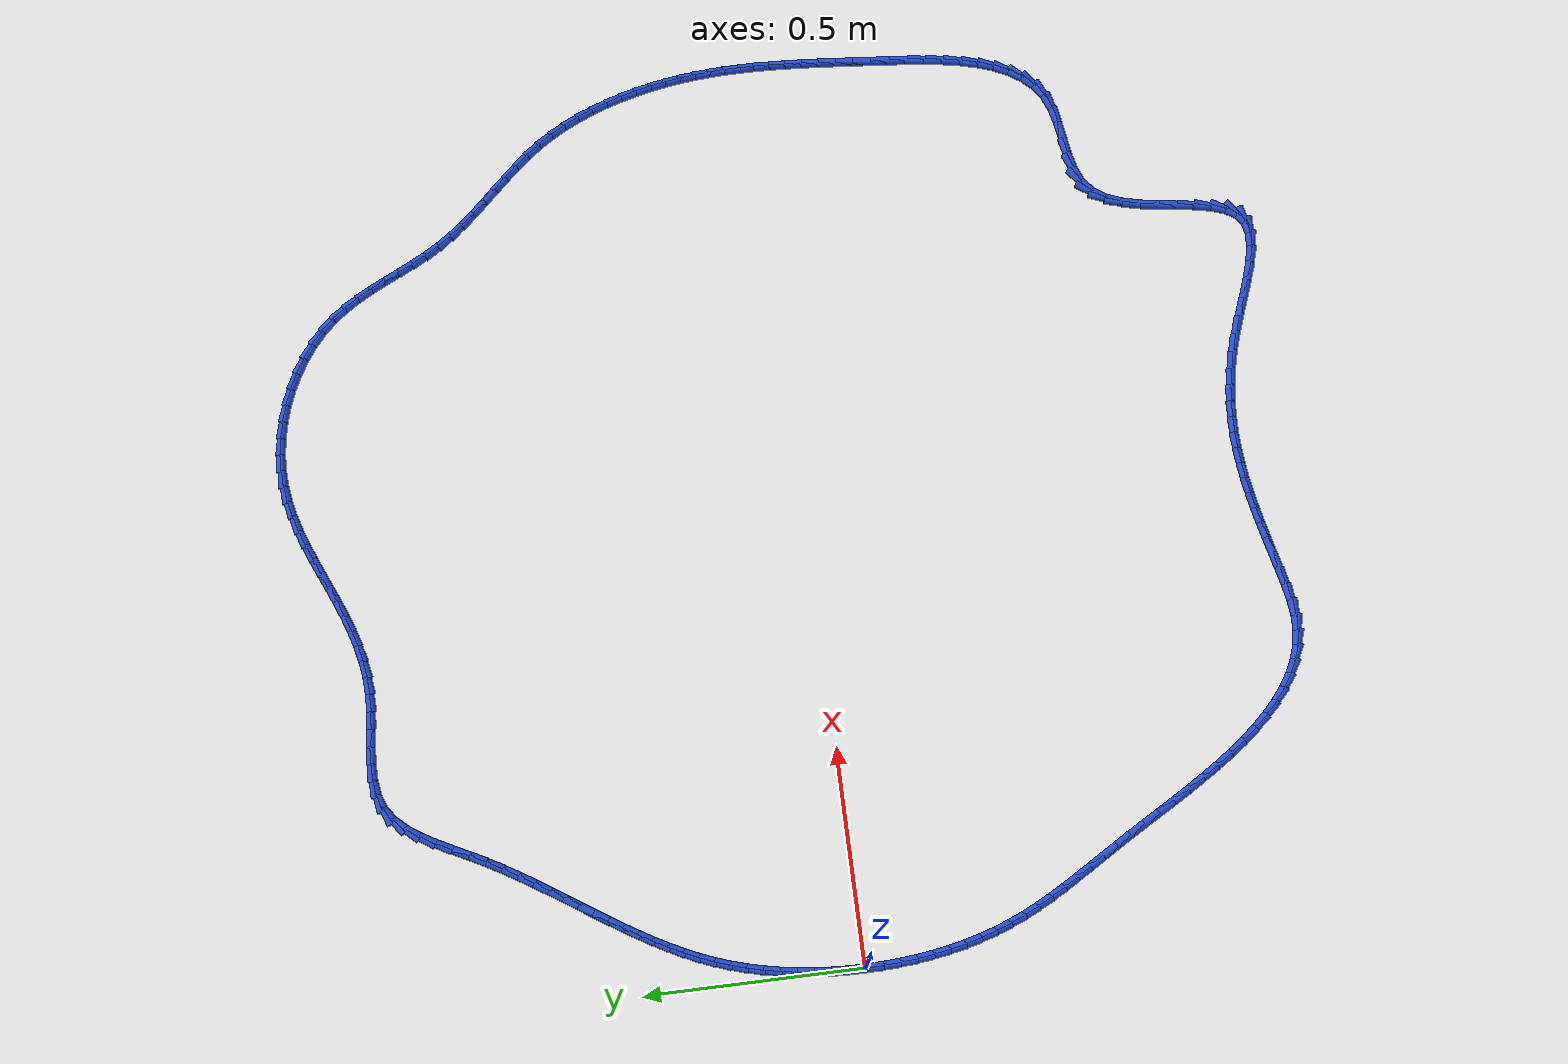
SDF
<sdf version="1.6">
 <world name="default">
  <light name="sun" type="directional">
   <pose>0 0 10 0 -0 0</pose>
   <diffuse>0.8 0.8 0.8 1</diffuse>
   <specular>0.2 0.2 0.2 1</specular>
   <attenuation>
    <range>1000</range>
    <constant>0.9</constant>
    <linear>0.01</linear>
    <quadratic>0.001</quadratic>
   </attenuation>
   <direction>-0.5 0.1 -0.9</direction>
  </light>
  <model name="ground_plane">
   <static>1</static>
   <link name="link">
    <collision name="collision">
     <geometry><plane><normal>0 0 1</normal><size>100 100</size></plane></geometry>
     <surface><friction><ode><mu>100</mu><mu2>50</mu2></ode></friction></surface>
    </collision>
    <visual name="visual">
     <cast_shadows>0</cast_shadows>
     <geometry><plane><normal>0 0 1</normal><size>100 100</size></plane></geometry>
     <material>
      <script><uri>file://media/materials/scripts/gazebo.material</uri><name>Gazebo/WhiteGlow</name></script>
     </material>
    </visual>
   </link>
  </model>
  <gravity>0 0 -9.8</gravity>
  <magnetic_field>6e-06 2.3e-05 -4.2e-05</magnetic_field>
  <atmosphere type="adiabatic"/>
  <physics name="default_physics" default="0" type="ode">
   <max_step_size>0.001</max_step_size>
   <real_time_factor>1</real_time_factor>
   <real_time_update_rate>1000</real_time_update_rate>
  </physics>
  <scene><ambient>0.4 0.4 0.4 1</ambient><background>0.7 0.7 0.7 1</background><shadows>1</shadows></scene>
  <spherical_coordinates>
   <surface_model>EARTH_WGS84</surface_model>
   <latitude_deg>0</latitude_deg>
   <longitude_deg>0</longitude_deg>
   <elevation>0</elevation>
   <heading_deg>0</heading_deg>
  </spherical_coordinates>
  <model name="line">
   <link name="link_0">
    <pose>-3.469446951953614e-18 4.163336342344337e-17 0.01 0 1.57 1.5526658345678408</pose>
    <collision name="collision">
     <geometry><cylinder><radius>0.01</radius><length>0.08</length></cylinder></geometry>
    </collision>
    <visual name="visual">
     <material>
      <script><name>Gazebo/Blue</name><uri>file://media/materials/scripts/gazebo.material</uri></script>
     </material>
     <geometry><cylinder><radius>0.01</radius><length>0.08</length></cylinder></geometry>
    </visual>
   </link>
   <link name="link_1">
    <pose>0.000692005057310479 0.03816384149387917 0.01 0 1.57 1.517928954553385</pose>
    <collision name="collision">
     <geometry><cylinder><radius>0.01</radius><length>0.08</length></cylinder></geometry>
    </collision>
    <visual name="visual">
     <material>
      <script><name>Gazebo/Blue</name><uri>file://media/materials/scripts/gazebo.material</uri></script>
     </material>
     <geometry><cylinder><radius>0.01</radius><length>0.08</length></cylinder></geometry>
    </visual>
   </link>
   <link name="link_2">
    <pose>0.002705376215841676 0.07621178979032595 0.01 0 1.57 1.4820772021216293</pose>
    <collision name="collision">
     <geometry><cylinder><radius>0.01</radius><length>0.08</length></cylinder></geometry>
    </collision>
    <visual name="visual">
     <material>
      <script><name>Gazebo/Blue</name><uri>file://media/materials/scripts/gazebo.material</uri></script>
     </material>
     <geometry><cylinder><radius>0.01</radius><length>0.08</length></cylinder></geometry>
    </visual>
   </link>
   <link name="link_3">
    <pose>0.006070062355582308 0.11403738385729371 0.01 0 1.57 1.4448962398728415</pose>
    <collision name="collision">
     <geometry><cylinder><radius>0.01</radius><length>0.08</length></cylinder></geometry>
    </collision>
    <visual name="visual">
     <material>
      <script><name>Gazebo/Blue</name><uri>file://media/materials/scripts/gazebo.material</uri></script>
     </material>
     <geometry><cylinder><radius>0.01</radius><length>0.08</length></cylinder></geometry>
    </visual>
   </link>
   <link name="link_4">
    <pose>0.010816012356521092 0.15153416266273562 0.01 0 1.57 1.4061663035214347</pose>
    <collision name="collision">
     <geometry><cylinder><radius>0.01</radius><length>0.08</length></cylinder></geometry>
    </collision>
    <visual name="visual">
     <material>
      <script><name>Gazebo/Blue</name><uri>file://media/materials/scripts/gazebo.material</uri></script>
     </material>
     <geometry><cylinder><radius>0.01</radius><length>0.08</length></cylinder></geometry>
    </visual>
   </link>
   <link name="link_5">
    <pose>0.016973175098646744 0.18859566517460494 0.01 0 1.57 1.365662337383973</pose>
    <collision name="collision">
     <geometry><cylinder><radius>0.01</radius><length>0.08</length></cylinder></geometry>
    </collision>
    <visual name="visual">
     <material>
      <script><name>Gazebo/Blue</name><uri>file://media/materials/scripts/gazebo.material</uri></script>
     </material>
     <geometry><cylinder><radius>0.01</radius><length>0.08</length></cylinder></geometry>
    </visual>
   </link>
   <link name="link_6">
    <pose>0.024571499461947983 0.22511543036085488 0.01 0 1.57 1.323155215370519</pose>
    <collision name="collision">
     <geometry><cylinder><radius>0.01</radius><length>0.08</length></cylinder></geometry>
    </collision>
    <visual name="visual">
     <material>
      <script><name>Gazebo/Blue</name><uri>file://media/materials/scripts/gazebo.material</uri></script>
     </material>
     <geometry><cylinder><radius>0.01</radius><length>0.08</length></cylinder></geometry>
    </visual>
   </link>
   <link name="link_7">
    <pose>0.03364093432641353 0.26098699718943874 0.01 0 1.57 1.2784143873026845</pose>
    <collision name="collision">
     <geometry><cylinder><radius>0.01</radius><length>0.08</length></cylinder></geometry>
    </collision>
    <visual name="visual">
     <material>
      <script><name>Gazebo/Blue</name><uri>file://media/materials/scripts/gazebo.material</uri></script>
     </material>
     <geometry><cylinder><radius>0.01</radius><length>0.08</length></cylinder></geometry>
    </visual>
   </link>
   <link name="link_8">
    <pose>0.04421142857203211 0.2961039046283098 0.01 0 1.57 1.2312176223736868</pose>
    <collision name="collision">
     <geometry><cylinder><radius>0.01</radius><length>0.08</length></cylinder></geometry>
    </collision>
    <visual name="visual">
     <material>
      <script><name>Gazebo/Blue</name><uri>file://media/materials/scripts/gazebo.material</uri></script>
     </material>
     <geometry><cylinder><radius>0.01</radius><length>0.08</length></cylinder></geometry>
    </visual>
   </link>
   <link name="link_9">
    <pose>0.05631279495881954 0.3303598798198596 0.01 0 1.57 1.1831923428890632</pose>
    <collision name="collision">
     <geometry><cylinder><radius>0.01</radius><length>0.08</length></cylinder></geometry>
    </collision>
    <visual name="visual">
     <material>
      <script><name>Gazebo/Blue</name><uri>file://media/materials/scripts/gazebo.material</uri></script>
     </material>
     <geometry><cylinder><radius>0.01</radius><length>0.08</length></cylinder></geometry>
    </visual>
   </link>
   <link name="link_10">
    <pose>0.06992902338415596 0.36371199616832356 0.01 0 1.57 1.1390213783947292</pose>
    <collision name="collision">
     <geometry><cylinder><radius>0.01</radius><length>0.08</length></cylinder></geometry>
    </collision>
    <visual name="visual">
     <material>
      <script><name>Gazebo/Blue</name><uri>file://media/materials/scripts/gazebo.material</uri></script>
     </material>
     <geometry><cylinder><radius>0.01</radius><length>0.08</length></cylinder></geometry>
    </visual>
   </link>
   <link name="link_11">
    <pose>0.08493192024140475 0.39627241135707675 0.01 0 1.57 1.0998427410901814</pose>
    <collision name="collision">
     <geometry><cylinder><radius>0.01</radius><length>0.08</length></cylinder></geometry>
    </collision>
    <visual name="visual">
     <material>
      <script><name>Gazebo/Blue</name><uri>file://media/materials/scripts/gazebo.material</uri></script>
     </material>
     <geometry><cylinder><radius>0.01</radius><length>0.08</length></cylinder></geometry>
    </visual>
   </link>
   <link name="link_12">
    <pose>0.10117644096385396 0.4281765781075573 0.01 0 1.57 1.0659921203746021</pose>
    <collision name="collision">
     <geometry><cylinder><radius>0.01</radius><length>0.08</length></cylinder></geometry>
    </collision>
    <visual name="visual">
     <material>
      <script><name>Gazebo/Blue</name><uri>file://media/materials/scripts/gazebo.material</uri></script>
     </material>
     <geometry><cylinder><radius>0.01</radius><length>0.08</length></cylinder></geometry>
    </visual>
   </link>
   <link name="link_13">
    <pose>0.11851754098479163 0.4595599491412029 0.01 0 1.57 1.0376713300870664</pose>
    <collision name="collision">
     <geometry><cylinder><radius>0.01</radius><length>0.08</length></cylinder></geometry>
    </collision>
    <visual name="visual">
     <material>
      <script><name>Gazebo/Blue</name><uri>file://media/materials/scripts/gazebo.material</uri></script>
     </material>
     <geometry><cylinder><radius>0.01</radius><length>0.08</length></cylinder></geometry>
    </visual>
   </link>
   <link name="link_14">
    <pose>0.13681017573750584 0.49055797717945193 0.01 0 1.57 1.0149722399550534</pose>
    <collision name="collision">
     <geometry><cylinder><radius>0.01</radius><length>0.08</length></cylinder></geometry>
    </collision>
    <visual name="visual">
     <material>
      <script><name>Gazebo/Blue</name><uri>file://media/materials/scripts/gazebo.material</uri></script>
     </material>
     <geometry><cylinder><radius>0.01</radius><length>0.08</length></cylinder></geometry>
    </visual>
   </link>
   <link name="link_15">
    <pose>0.15590930065528466 0.521306114943742 0.01 0 1.57 0.9979018036385471</pose>
    <collision name="collision">
     <geometry><cylinder><radius>0.01</radius><length>0.08</length></cylinder></geometry>
    </collision>
    <visual name="visual">
     <material>
      <script><name>Gazebo/Blue</name><uri>file://media/materials/scripts/gazebo.material</uri></script>
     </material>
     <geometry><cylinder><radius>0.01</radius><length>0.08</length></cylinder></geometry>
    </visual>
   </link>
   <link name="link_16">
    <pose>0.1756698711714162 0.5519398151555116 0.01 0 1.57 0.9864046569775238</pose>
    <collision name="collision">
     <geometry><cylinder><radius>0.01</radius><length>0.08</length></cylinder></geometry>
    </collision>
    <visual name="visual">
     <material>
      <script><name>Gazebo/Blue</name><uri>file://media/materials/scripts/gazebo.material</uri></script>
     </material>
     <geometry><cylinder><radius>0.01</radius><length>0.08</length></cylinder></geometry>
    </visual>
   </link>
   <link name="link_17">
    <pose>0.19594684271918847 0.5825945305361981 0.01 0 1.57 0.9803812774716737</pose>
    <collision name="collision">
     <geometry><cylinder><radius>0.01</radius><length>0.08</length></cylinder></geometry>
    </collision>
    <visual name="visual">
     <material>
      <script><name>Gazebo/Blue</name><uri>file://media/materials/scripts/gazebo.material</uri></script>
     </material>
     <geometry><cylinder><radius>0.01</radius><length>0.08</length></cylinder></geometry>
    </visual>
   </link>
   <link name="link_18">
    <pose>0.21659517073188952 0.61340571380724 0.01 0 1.57 0.9797009127073677</pose>
    <collision name="collision">
     <geometry><cylinder><radius>0.01</radius><length>0.08</length></cylinder></geometry>
    </collision>
    <visual name="visual">
     <material>
      <script><name>Gazebo/Blue</name><uri>file://media/materials/scripts/gazebo.material</uri></script>
     </material>
     <geometry><cylinder><radius>0.01</radius><length>0.08</length></cylinder></geometry>
    </visual>
   </link>
   <link name="link_19">
    <pose>0.2374698106428074 0.6445088176900747 0.01 0 1.57 0.9842093128487828</pose>
    <collision name="collision">
     <geometry><cylinder><radius>0.01</radius><length>0.08</length></cylinder></geometry>
    </collision>
    <visual name="visual">
     <material>
      <script><name>Gazebo/Blue</name><uri>file://media/materials/scripts/gazebo.material</uri></script>
     </material>
     <geometry><cylinder><radius>0.01</radius><length>0.08</length></cylinder></geometry>
    </visual>
   </link>
   <link name="link_20">
    <pose>0.2584257178852303 0.6760392949061407 0.01 0 1.57 0.9937317985861548</pose>
    <collision name="collision">
     <geometry><cylinder><radius>0.01</radius><length>0.08</length></cylinder></geometry>
    </collision>
    <visual name="visual">
     <material>
      <script><name>Gazebo/Blue</name><uri>file://media/materials/scripts/gazebo.material</uri></script>
     </material>
     <geometry><cylinder><radius>0.01</radius><length>0.08</length></cylinder></geometry>
    </visual>
   </link>
   <link name="link_21">
    <pose>0.2793178478924462 0.7081325981768758 0.01 0 1.57 1.0080724723834482</pose>
    <collision name="collision">
     <geometry><cylinder><radius>0.01</radius><length>0.08</length></cylinder></geometry>
    </collision>
    <visual name="visual">
     <material>
      <script><name>Gazebo/Blue</name><uri>file://media/materials/scripts/gazebo.material</uri></script>
     </material>
     <geometry><cylinder><radius>0.01</radius><length>0.08</length></cylinder></geometry>
    </visual>
   </link>
   <link name="link_22">
    <pose>0.3000011560977432 0.7409241802237181 0.01 0 1.57 1.0270105432330627</pose>
    <collision name="collision">
     <geometry><cylinder><radius>0.01</radius><length>0.08</length></cylinder></geometry>
    </collision>
    <visual name="visual">
     <material>
      <script><name>Gazebo/Blue</name><uri>file://media/materials/scripts/gazebo.material</uri></script>
     </material>
     <geometry><cylinder><radius>0.01</radius><length>0.08</length></cylinder></geometry>
    </visual>
   </link>
   <link name="link_23">
    <pose>0.3203305979344093 0.7745494937681054 0.01 0 1.57 1.0502948557643872</pose>
    <collision name="collision">
     <geometry><cylinder><radius>0.01</radius><length>0.08</length></cylinder></geometry>
    </collision>
    <visual name="visual">
     <material>
      <script><name>Gazebo/Blue</name><uri>file://media/materials/scripts/gazebo.material</uri></script>
     </material>
     <geometry><cylinder><radius>0.01</radius><length>0.08</length></cylinder></geometry>
    </visual>
   </link>
   <link name="link_24">
    <pose>0.3401611288357326 0.8091439915314756 0.01 0 1.57 1.0776150927210633</pose>
    <collision name="collision">
     <geometry><cylinder><radius>0.01</radius><length>0.08</length></cylinder></geometry>
    </collision>
    <visual name="visual">
     <material>
      <script><name>Gazebo/Blue</name><uri>file://media/materials/scripts/gazebo.material</uri></script>
     </material>
     <geometry><cylinder><radius>0.01</radius><length>0.08</length></cylinder></geometry>
    </visual>
   </link>
   <link name="link_25">
    <pose>0.35934824108856933 0.8448421791879832 0.01 0 1.57 1.0989478587985846</pose>
    <collision name="collision">
     <geometry><cylinder><radius>0.01</radius><length>0.08</length></cylinder></geometry>
    </collision>
    <visual name="visual">
     <material>
      <script><name>Gazebo/Blue</name><uri>file://media/materials/scripts/gazebo.material</uri></script>
     </material>
     <geometry><cylinder><radius>0.01</radius><length>0.08</length></cylinder></geometry>
    </visual>
   </link>
   <link name="link_26">
    <pose>0.37798382966204236 0.8813615315279394 0.01 0 1.57 1.089783607153572</pose>
    <collision name="collision">
     <geometry><cylinder><radius>0.01</radius><length>0.08</length></cylinder></geometry>
    </collision>
    <visual name="visual">
     <material>
      <script><name>Gazebo/Blue</name><uri>file://media/materials/scripts/gazebo.material</uri></script>
     </material>
     <geometry><cylinder><radius>0.01</radius><length>0.08</length></cylinder></geometry>
    </visual>
   </link>
   <link name="link_27">
    <pose>0.3967661203142834 0.9173499133760711 0.01 0 1.57 1.0443293523876431</pose>
    <collision name="collision">
     <geometry><cylinder><radius>0.01</radius><length>0.08</length></cylinder></geometry>
    </collision>
    <visual name="visual">
     <material>
      <script><name>Gazebo/Blue</name><uri>file://media/materials/scripts/gazebo.material</uri></script>
     </material>
     <geometry><cylinder><radius>0.01</radius><length>0.08</length></cylinder></geometry>
    </visual>
   </link>
   <link name="link_28">
    <pose>0.4164891871219519 0.9512861064121658 0.01 0 1.57 0.9555760790746389</pose>
    <collision name="collision">
     <geometry><cylinder><radius>0.01</radius><length>0.08</length></cylinder></geometry>
    </collision>
    <visual name="visual">
     <material>
      <script><name>Gazebo/Blue</name><uri>file://media/materials/scripts/gazebo.material</uri></script>
     </material>
     <geometry><cylinder><radius>0.01</radius><length>0.08</length></cylinder></geometry>
    </visual>
   </link>
   <link name="link_29">
    <pose>0.4379471041617067 0.9816488923160097 0.01 0 1.57 0.8114062872159397</pose>
    <collision name="collision">
     <geometry><cylinder><radius>0.01</radius><length>0.08</length></cylinder></geometry>
    </collision>
    <visual name="visual">
     <material>
      <script><name>Gazebo/Blue</name><uri>file://media/materials/scripts/gazebo.material</uri></script>
     </material>
     <geometry><cylinder><radius>0.01</radius><length>0.08</length></cylinder></geometry>
    </visual>
   </link>
   <link name="link_30">
    <pose>0.4619339455102066 1.0069170527673887 0.01 0 1.57 0.599223776304519</pose>
    <collision name="collision">
     <geometry><cylinder><radius>0.01</radius><length>0.08</length></cylinder></geometry>
    </collision>
    <visual name="visual">
     <material>
      <script><name>Gazebo/Blue</name><uri>file://media/materials/scripts/gazebo.material</uri></script>
     </material>
     <geometry><cylinder><radius>0.01</radius><length>0.08</length></cylinder></geometry>
    </visual>
   </link>
   <link name="link_31">
    <pose>0.48924369632827963 1.0255695547623456 0.01 0 1.57 0.34449556823501687</pose>
    <collision name="collision">
     <geometry><cylinder><radius>0.01</radius><length>0.08</length></cylinder></geometry>
    </collision>
    <visual name="visual">
     <material>
      <script><name>Gazebo/Blue</name><uri>file://media/materials/scripts/gazebo.material</uri></script>
     </material>
     <geometry><cylinder><radius>0.01</radius><length>0.08</length></cylinder></geometry>
    </visual>
   </link>
   <link name="link_32">
    <pose>0.5203591781723657 1.0367338850592747 0.01 0 1.57 0.1416656107038731</pose>
    <collision name="collision">
     <geometry><cylinder><radius>0.01</radius><length>0.08</length></cylinder></geometry>
    </collision>
    <visual name="visual">
     <material>
      <script><name>Gazebo/Blue</name><uri>file://media/materials/scripts/gazebo.material</uri></script>
     </material>
     <geometry><cylinder><radius>0.01</radius><length>0.08</length></cylinder></geometry>
    </visual>
   </link>
   <link name="link_33">
    <pose>0.554754718013593 1.0416394107765536 0.01 0 1.57 0.008150989017048915</pose>
    <collision name="collision">
     <geometry><cylinder><radius>0.01</radius><length>0.08</length></cylinder></geometry>
    </collision>
    <visual name="visual">
     <material>
      <script><name>Gazebo/Blue</name><uri>file://media/materials/scripts/gazebo.material</uri></script>
     </material>
     <geometry><cylinder><radius>0.01</radius><length>0.08</length></cylinder></geometry>
    </visual>
   </link>
   <link name="link_34">
    <pose>0.5917006942937225 1.0419405636928616 0.01 0 1.57 -0.06822018546219824</pose>
    <collision name="collision">
     <geometry><cylinder><radius>0.01</radius><length>0.08</length></cylinder></geometry>
    </collision>
    <visual name="visual">
     <material>
      <script><name>Gazebo/Blue</name><uri>file://media/materials/scripts/gazebo.material</uri></script>
     </material>
     <geometry><cylinder><radius>0.01</radius><length>0.08</length></cylinder></geometry>
    </visual>
   </link>
   <link name="link_35">
    <pose>0.6304674854545147 1.0392917755868796 0.01 0 1.57 -0.09863763149952001</pose>
    <collision name="collision">
     <geometry><cylinder><radius>0.01</radius><length>0.08</length></cylinder></geometry>
    </collision>
    <visual name="visual">
     <material>
      <script><name>Gazebo/Blue</name><uri>file://media/materials/scripts/gazebo.material</uri></script>
     </material>
     <geometry><cylinder><radius>0.01</radius><length>0.08</length></cylinder></geometry>
    </visual>
   </link>
   <link name="link_36">
    <pose>0.6703254699377308 1.0353474782372865 0.01 0 1.57 -0.08891004050234656</pose>
    <collision name="collision">
     <geometry><cylinder><radius>0.01</radius><length>0.08</length></cylinder></geometry>
    </collision>
    <visual name="visual">
     <material>
      <script><name>Gazebo/Blue</name><uri>file://media/materials/scripts/gazebo.material</uri></script>
     </material>
     <geometry><cylinder><radius>0.01</radius><length>0.08</length></cylinder></geometry>
    </visual>
   </link>
   <link name="link_37">
    <pose>0.7105450261851314 1.0317621034227638 0.01 0 1.57 -0.03942651141357657</pose>
    <collision name="collision">
     <geometry><cylinder><radius>0.01</radius><length>0.08</length></cylinder></geometry>
    </collision>
    <visual name="visual">
     <material>
      <script><name>Gazebo/Blue</name><uri>file://media/materials/scripts/gazebo.material</uri></script>
     </material>
     <geometry><cylinder><radius>0.01</radius><length>0.08</length></cylinder></geometry>
    </visual>
   </link>
   <link name="link_38">
    <pose>0.7503965326384775 1.0301900829219903 0.01 0 1.57 0.04745717436360032</pose>
    <collision name="collision">
     <geometry><cylinder><radius>0.01</radius><length>0.08</length></cylinder></geometry>
    </collision>
    <visual name="visual">
     <material>
      <script><name>Gazebo/Blue</name><uri>file://media/materials/scripts/gazebo.material</uri></script>
     </material>
     <geometry><cylinder><radius>0.01</radius><length>0.08</length></cylinder></geometry>
    </visual>
   </link>
   <link name="link_39">
    <pose>0.7892511844399216 1.032035400446579 0.01 0 1.57 0.1378227707298543</pose>
    <collision name="collision">
     <geometry><cylinder><radius>0.01</radius><length>0.08</length></cylinder></geometry>
    </collision>
    <visual name="visual">
     <material>
      <script><name>Gazebo/Blue</name><uri>file://media/materials/scripts/gazebo.material</uri></script>
     </material>
     <geometry><cylinder><radius>0.01</radius><length>0.08</length></cylinder></geometry>
    </visual>
   </link>
   <link name="link_40">
    <pose>0.8270531695498331 1.0372786153825326 0.01 0 1.57 0.21661271451964845</pose>
    <collision name="collision">
     <geometry><cylinder><radius>0.01</radius><length>0.08</length></cylinder></geometry>
    </collision>
    <visual name="visual">
     <material>
      <script><name>Gazebo/Blue</name><uri>file://media/materials/scripts/gazebo.material</uri></script>
     </material>
     <geometry><cylinder><radius>0.01</radius><length>0.08</length></cylinder></geometry>
    </visual>
   </link>
   <link name="link_41">
    <pose>0.8639488384059547 1.045398076653747 0.01 0 1.57 0.2821059720336501</pose>
    <collision name="collision">
     <geometry><cylinder><radius>0.01</radius><length>0.08</length></cylinder></geometry>
    </collision>
    <visual name="visual">
     <material>
      <script><name>Gazebo/Blue</name><uri>file://media/materials/scripts/gazebo.material</uri></script>
     </material>
     <geometry><cylinder><radius>0.01</radius><length>0.08</length></cylinder></geometry>
    </visual>
   </link>
   <link name="link_42">
    <pose>0.9000847704980969 1.055871564174742 0.01 0 1.57 0.333469239236096</pose>
    <collision name="collision">
     <geometry><cylinder><radius>0.01</radius><length>0.08</length></cylinder></geometry>
    </collision>
    <visual name="visual">
     <material>
      <script><name>Gazebo/Blue</name><uri>file://media/materials/scripts/gazebo.material</uri></script>
     </material>
     <geometry><cylinder><radius>0.01</radius><length>0.08</length></cylinder></geometry>
    </visual>
   </link>
   <link name="link_43">
    <pose>0.9356075453160714 1.068176857860039 0.01 0 1.57 0.3704430767512039</pose>
    <collision name="collision">
     <geometry><cylinder><radius>0.01</radius><length>0.08</length></cylinder></geometry>
    </collision>
    <visual name="visual">
     <material>
      <script><name>Gazebo/Blue</name><uri>file://media/materials/scripts/gazebo.material</uri></script>
     </material>
     <geometry><cylinder><radius>0.01</radius><length>0.08</length></cylinder></geometry>
    </visual>
   </link>
   <link name="link_44">
    <pose>0.9706637423496896 1.081791737624158 0.01 0 1.57 0.39304405741044196</pose>
    <collision name="collision">
     <geometry><cylinder><radius>0.01</radius><length>0.08</length></cylinder></geometry>
    </collision>
    <visual name="visual">
     <material>
      <script><name>Gazebo/Blue</name><uri>file://media/materials/scripts/gazebo.material</uri></script>
     </material>
     <geometry><cylinder><radius>0.01</radius><length>0.08</length></cylinder></geometry>
    </visual>
   </link>
   <link name="link_45">
    <pose>1.0053999410887617 1.0961939833816188 0.01 0 1.57 0.40133653675243447</pose>
    <collision name="collision">
     <geometry><cylinder><radius>0.01</radius><length>0.08</length></cylinder></geometry>
    </collision>
    <visual name="visual">
     <material>
      <script><name>Gazebo/Blue</name><uri>file://media/materials/scripts/gazebo.material</uri></script>
     </material>
     <geometry><cylinder><radius>0.01</radius><length>0.08</length></cylinder></geometry>
    </visual>
   </link>
   <link name="link_46">
    <pose>1.0399627210230997 1.1108613750469418 0.01 0 1.57 0.39529289837999454</pose>
    <collision name="collision">
     <geometry><cylinder><radius>0.01</radius><length>0.08</length></cylinder></geometry>
    </collision>
    <visual name="visual">
     <material>
      <script><name>Gazebo/Blue</name><uri>file://media/materials/scripts/gazebo.material</uri></script>
     </material>
     <geometry><cylinder><radius>0.01</radius><length>0.08</length></cylinder></geometry>
    </visual>
   </link>
   <link name="link_47">
    <pose>1.0744986616425147 1.1252716925346478 0.01 0 1.57 0.3747407939037958</pose>
    <collision name="collision">
     <geometry><cylinder><radius>0.01</radius><length>0.08</length></cylinder></geometry>
    </collision>
    <visual name="visual">
     <material>
      <script><name>Gazebo/Blue</name><uri>file://media/materials/scripts/gazebo.material</uri></script>
     </material>
     <geometry><cylinder><radius>0.01</radius><length>0.08</length></cylinder></geometry>
    </visual>
   </link>
   <link name="link_48">
    <pose>1.1091543424368173 1.138902715759256 0.01 0 1.57 0.33939693262611903</pose>
    <collision name="collision">
     <geometry><cylinder><radius>0.01</radius><length>0.08</length></cylinder></geometry>
    </collision>
    <visual name="visual">
     <material>
      <script><name>Gazebo/Blue</name><uri>file://media/materials/scripts/gazebo.material</uri></script>
     </material>
     <geometry><cylinder><radius>0.01</radius><length>0.08</length></cylinder></geometry>
    </visual>
   </link>
   <link name="link_49">
    <pose>1.1440763428958185 1.1512322246352873 0.01 0 1.57 0.28899632323896146</pose>
    <collision name="collision">
     <geometry><cylinder><radius>0.01</radius><length>0.08</length></cylinder></geometry>
    </collision>
    <visual name="visual">
     <material>
      <script><name>Gazebo/Blue</name><uri>file://media/materials/scripts/gazebo.material</uri></script>
     </material>
     <geometry><cylinder><radius>0.01</radius><length>0.08</length></cylinder></geometry>
    </visual>
   </link>
   <link name="link_50">
    <pose>1.1794112425093306 1.1617379990772623 0.01 0 1.57 0.22352975985347273</pose>
    <collision name="collision">
     <geometry><cylinder><radius>0.01</radius><length>0.08</length></cylinder></geometry>
    </collision>
    <visual name="visual">
     <material>
      <script><name>Gazebo/Blue</name><uri>file://media/materials/scripts/gazebo.material</uri></script>
     </material>
     <geometry><cylinder><radius>0.01</radius><length>0.08</length></cylinder></geometry>
    </visual>
   </link>
   <link name="link_51">
    <pose>1.2153056207671642 1.169897818999701 0.01 0 1.57 0.1435838207664179</pose>
    <collision name="collision">
     <geometry><cylinder><radius>0.01</radius><length>0.08</length></cylinder></geometry>
    </collision>
    <visual name="visual">
     <material>
      <script><name>Gazebo/Blue</name><uri>file://media/materials/scripts/gazebo.material</uri></script>
     </material>
     <geometry><cylinder><radius>0.01</radius><length>0.08</length></cylinder></geometry>
    </visual>
   </link>
   <link name="link_52">
    <pose>1.2519060571591303 1.1751894643171232 0.01 0 1.57 0.05170180035285921</pose>
    <collision name="collision">
     <geometry><cylinder><radius>0.01</radius><length>0.08</length></cylinder></geometry>
    </collision>
    <visual name="visual">
     <material>
      <script><name>Gazebo/Blue</name><uri>file://media/materials/scripts/gazebo.material</uri></script>
     </material>
     <geometry><cylinder><radius>0.01</radius><length>0.08</length></cylinder></geometry>
    </visual>
   </link>
   <link name="link_53">
    <pose>1.2893290171514358 1.1771260245551687 0.01 0 1.57 -0.04019247868033696</pose>
    <collision name="collision">
     <geometry><cylinder><radius>0.01</radius><length>0.08</length></cylinder></geometry>
    </collision>
    <visual name="visual">
     <material>
      <script><name>Gazebo/Blue</name><uri>file://media/materials/scripts/gazebo.material</uri></script>
     </material>
     <geometry><cylinder><radius>0.01</radius><length>0.08</length></cylinder></geometry>
    </visual>
   </link>
   <link name="link_54">
    <pose>1.327370611659627 1.1755962147205774 0.01 0 1.57 -0.12687189911592808</pose>
    <collision name="collision">
     <geometry><cylinder><radius>0.01</radius><length>0.08</length></cylinder></geometry>
    </collision>
    <visual name="visual">
     <material>
      <script><name>Gazebo/Blue</name><uri>file://media/materials/scripts/gazebo.material</uri></script>
     </material>
     <geometry><cylinder><radius>0.01</radius><length>0.08</length></cylinder></geometry>
    </visual>
   </link>
   <link name="link_55">
    <pose>1.365633561072937 1.170715506110381 0.01 0 1.57 -0.20988967936663516</pose>
    <collision name="collision">
     <geometry><cylinder><radius>0.01</radius><length>0.08</length></cylinder></geometry>
    </collision>
    <visual name="visual">
     <material>
      <script><name>Gazebo/Blue</name><uri>file://media/materials/scripts/gazebo.material</uri></script>
     </material>
     <geometry><cylinder><radius>0.01</radius><length>0.08</length></cylinder></geometry>
    </visual>
   </link>
   <link name="link_56">
    <pose>1.4037179103230653 1.1626025070771708 0.01 0 1.57 -0.29084375874761764</pose>
    <collision name="collision">
     <geometry><cylinder><radius>0.01</radius><length>0.08</length></cylinder></geometry>
    </collision>
    <visual name="visual">
     <material>
      <script><name>Gazebo/Blue</name><uri>file://media/materials/scripts/gazebo.material</uri></script>
     </material>
     <geometry><cylinder><radius>0.01</radius><length>0.08</length></cylinder></geometry>
    </visual>
   </link>
   <link name="link_57">
    <pose>1.4412237043417104 1.1513758259735356 0.01 0 1.57 -0.3712883608198027</pose>
    <collision name="collision">
     <geometry><cylinder><radius>0.01</radius><length>0.08</length></cylinder></geometry>
    </collision>
    <visual name="visual">
     <material>
      <script><name>Gazebo/Blue</name><uri>file://media/materials/scripts/gazebo.material</uri></script>
     </material>
     <geometry><cylinder><radius>0.01</radius><length>0.08</length></cylinder></geometry>
    </visual>
   </link>
   <link name="link_58">
    <pose>1.4777509880605717 1.1371540711520656 0.01 0 1.57 -0.45275075055291514</pose>
    <collision name="collision">
     <geometry><cylinder><radius>0.01</radius><length>0.08</length></cylinder></geometry>
    </collision>
    <visual name="visual">
     <material>
      <script><name>Gazebo/Blue</name><uri>file://media/materials/scripts/gazebo.material</uri></script>
     </material>
     <geometry><cylinder><radius>0.01</radius><length>0.08</length></cylinder></geometry>
    </visual>
   </link>
   <link name="link_59">
    <pose>1.5128998064113477 1.1200558509653507 0.01 0 1.57 -0.5367501989448316</pose>
    <collision name="collision">
     <geometry><cylinder><radius>0.01</radius><length>0.08</length></cylinder></geometry>
    </collision>
    <visual name="visual">
     <material>
      <script><name>Gazebo/Blue</name><uri>file://media/materials/scripts/gazebo.material</uri></script>
     </material>
     <geometry><cylinder><radius>0.01</radius><length>0.08</length></cylinder></geometry>
    </visual>
   </link>
   <link name="link_60">
    <pose>1.5462702043257381 1.1001997737659808 0.01 0 1.57 -0.624805301709084</pose>
    <collision name="collision">
     <geometry><cylinder><radius>0.01</radius><length>0.08</length></cylinder></geometry>
    </collision>
    <visual name="visual">
     <material>
      <script><name>Gazebo/Blue</name><uri>file://media/materials/scripts/gazebo.material</uri></script>
     </material>
     <geometry><cylinder><radius>0.01</radius><length>0.08</length></cylinder></geometry>
    </visual>
   </link>
   <link name="link_61">
    <pose>1.5774622267354417 1.0777044479065458 0.01 0 1.57 -0.718413899002882</pose>
    <collision name="collision">
     <geometry><cylinder><radius>0.01</radius><length>0.08</length></cylinder></geometry>
    </collision>
    <visual name="visual">
     <material>
      <script><name>Gazebo/Blue</name><uri>file://media/materials/scripts/gazebo.material</uri></script>
     </material>
     <geometry><cylinder><radius>0.01</radius><length>0.08</length></cylinder></geometry>
    </visual>
   </link>
   <link name="link_62">
    <pose>1.6060759185721571 1.0526884817396358 0.01 0 1.57 -0.818981354128782</pose>
    <collision name="collision">
     <geometry><cylinder><radius>0.01</radius><length>0.08</length></cylinder></geometry>
    </collision>
    <visual name="visual">
     <material>
      <script><name>Gazebo/Blue</name><uri>file://media/materials/scripts/gazebo.material</uri></script>
     </material>
     <geometry><cylinder><radius>0.01</radius><length>0.08</length></cylinder></geometry>
    </visual>
   </link>
   <link name="link_63">
    <pose>1.6317114873035357 1.0252705366099668 0.01 0 1.57 -0.9213576960967687</pose>
    <collision name="collision">
     <geometry><cylinder><radius>0.01</radius><length>0.08</length></cylinder></geometry>
    </collision>
    <visual name="visual">
     <material>
      <script><name>Gazebo/Blue</name><uri>file://media/materials/scripts/gazebo.material</uri></script>
     </material>
     <geometry><cylinder><radius>0.01</radius><length>0.08</length></cylinder></geometry>
    </visual>
   </link>
   <link name="link_64">
    <pose>1.6542056651810808 0.995646388808006 0.01 0 1.57 -1.005988973052637</pose>
    <collision name="collision">
     <geometry><cylinder><radius>0.01</radius><length>0.08</length></cylinder></geometry>
    </collision>
    <visual name="visual">
     <material>
      <script><name>Gazebo/Blue</name><uri>file://media/materials/scripts/gazebo.material</uri></script>
     </material>
     <geometry><cylinder><radius>0.01</radius><length>0.08</length></cylinder></geometry>
    </visual>
   </link>
   <link name="link_65">
    <pose>1.674104833376922 0.9642431837734752 0.01 0 1.57 -1.068152017973263</pose>
    <collision name="collision">
     <geometry><cylinder><radius>0.01</radius><length>0.08</length></cylinder></geometry>
    </collision>
    <visual name="visual">
     <material>
      <script><name>Gazebo/Blue</name><uri>file://media/materials/scripts/gazebo.material</uri></script>
     </material>
     <geometry><cylinder><radius>0.01</radius><length>0.08</length></cylinder></geometry>
    </visual>
   </link>
   <link name="link_66">
    <pose>1.692087907955173 0.9315312777286583 0.01 0 1.57 -1.1078459066383999</pose>
    <collision name="collision">
     <geometry><cylinder><radius>0.01</radius><length>0.08</length></cylinder></geometry>
    </collision>
    <visual name="visual">
     <material>
      <script><name>Gazebo/Blue</name><uri>file://media/materials/scripts/gazebo.material</uri></script>
     </material>
     <geometry><cylinder><radius>0.01</radius><length>0.08</length></cylinder></geometry>
    </visual>
   </link>
   <link name="link_67">
    <pose>1.7088338049799467 0.8979810268958368 0.01 0 1.57 -1.1255100529656163</pose>
    <collision name="collision">
     <geometry><cylinder><radius>0.01</radius><length>0.08</length></cylinder></geometry>
    </collision>
    <visual name="visual">
     <material>
      <script><name>Gazebo/Blue</name><uri>file://media/materials/scripts/gazebo.material</uri></script>
     </material>
     <geometry><cylinder><radius>0.01</radius><length>0.08</length></cylinder></geometry>
    </visual>
   </link>
   <link name="link_68">
    <pose>1.7250214405153563 0.864062787497295 0.01 0 1.57 -1.1214352253838764</pose>
    <collision name="collision">
     <geometry><cylinder><radius>0.01</radius><length>0.08</length></cylinder></geometry>
    </collision>
    <visual name="visual">
     <material>
      <script><name>Gazebo/Blue</name><uri>file://media/materials/scripts/gazebo.material</uri></script>
     </material>
     <geometry><cylinder><radius>0.01</radius><length>0.08</length></cylinder></geometry>
    </visual>
   </link>
   <link name="link_69">
    <pose>1.7413297306255167 0.8302469157553164 0.01 0 1.57 -1.0955147735487039</pose>
    <collision name="collision">
     <geometry><cylinder><radius>0.01</radius><length>0.08</length></cylinder></geometry>
    </collision>
    <visual name="visual">
     <material>
      <script><name>Gazebo/Blue</name><uri>file://media/materials/scripts/gazebo.material</uri></script>
     </material>
     <geometry><cylinder><radius>0.01</radius><length>0.08</length></cylinder></geometry>
    </visual>
   </link>
   <link name="link_70">
    <pose>1.7584375913745403 0.7970037678921844 0.01 0 1.57 -1.0472993505591395</pose>
    <collision name="collision">
     <geometry><cylinder><radius>0.01</radius><length>0.08</length></cylinder></geometry>
    </collision>
    <visual name="visual">
     <material>
      <script><name>Gazebo/Blue</name><uri>file://media/materials/scripts/gazebo.material</uri></script>
     </material>
     <geometry><cylinder><radius>0.01</radius><length>0.08</length></cylinder></geometry>
    </visual>
   </link>
   <link name="link_71">
    <pose>1.7770239388265407 0.7648037001301817 0.01 0 1.57 -0.9795043886562832</pose>
    <collision name="collision">
     <geometry><cylinder><radius>0.01</radius><length>0.08</length></cylinder></geometry>
    </collision>
    <visual name="visual">
     <material>
      <script><name>Gazebo/Blue</name><uri>file://media/materials/scripts/gazebo.material</uri></script>
     </material>
     <geometry><cylinder><radius>0.01</radius><length>0.08</length></cylinder></geometry>
    </visual>
   </link>
   <link name="link_72">
    <pose>1.7976727484136092 0.7340501454820897 0.01 0 1.57 -0.9164854564134749</pose>
    <collision name="collision">
     <geometry><cylinder><radius>0.01</radius><length>0.08</length></cylinder></geometry>
    </collision>
    <visual name="visual">
     <material>
      <script><name>Gazebo/Blue</name><uri>file://media/materials/scripts/gazebo.material</uri></script>
     </material>
     <geometry><cylinder><radius>0.01</radius><length>0.08</length></cylinder></geometry>
    </visual>
   </link>
   <link name="link_73">
    <pose>1.820237574278463 0.7046316663944021 0.01 0 1.57 -0.8698512085634424</pose>
    <collision name="collision">
     <geometry><cylinder><radius>0.01</radius><length>0.08</length></cylinder></geometry>
    </collision>
    <visual name="visual">
     <material>
      <script><name>Gazebo/Blue</name><uri>file://media/materials/scripts/gazebo.material</uri></script>
     </material>
     <geometry><cylinder><radius>0.01</radius><length>0.08</length></cylinder></geometry>
    </visual>
   </link>
   <link name="link_74">
    <pose>1.8442329948593525 0.6761978829176862 0.01 0 1.57 -0.8396126801246732</pose>
    <collision name="collision">
     <geometry><cylinder><radius>0.01</radius><length>0.08</length></cylinder></geometry>
    </collision>
    <visual name="visual">
     <material>
      <script><name>Gazebo/Blue</name><uri>file://media/materials/scripts/gazebo.material</uri></script>
     </material>
     <geometry><cylinder><radius>0.01</radius><length>0.08</length></cylinder></geometry>
    </visual>
   </link>
   <link name="link_75">
    <pose>1.8691717247500155 0.6483971012871915 0.01 0 1.57 -0.8255306388529394</pose>
    <collision name="collision">
     <geometry><cylinder><radius>0.01</radius><length>0.08</length></cylinder></geometry>
    </collision>
    <visual name="visual">
     <material>
      <script><name>Gazebo/Blue</name><uri>file://media/materials/scripts/gazebo.material</uri></script>
     </material>
     <geometry><cylinder><radius>0.01</radius><length>0.08</length></cylinder></geometry>
    </visual>
   </link>
   <link name="link_76">
    <pose>1.8945664785441898 0.6208776277381679 0.01 0 1.57 -0.8274173448622614</pose>
    <collision name="collision">
     <geometry><cylinder><radius>0.01</radius><length>0.08</length></cylinder></geometry>
    </collision>
    <visual name="visual">
     <material>
      <script><name>Gazebo/Blue</name><uri>file://media/materials/scripts/gazebo.material</uri></script>
     </material>
     <geometry><cylinder><radius>0.01</radius><length>0.08</length></cylinder></geometry>
    </visual>
   </link>
   <link name="link_77">
    <pose>1.919929970835616 0.5932877685058645 0.01 0 1.57 -0.8452430008218402</pose>
    <collision name="collision">
     <geometry><cylinder><radius>0.01</radius><length>0.08</length></cylinder></geometry>
    </collision>
    <visual name="visual">
     <material>
      <script><name>Gazebo/Blue</name><uri>file://media/materials/scripts/gazebo.material</uri></script>
     </material>
     <geometry><cylinder><radius>0.01</radius><length>0.08</length></cylinder></geometry>
    </visual>
   </link>
   <link name="link_78">
    <pose>1.944774916218031 0.5652758298255309 0.01 0 1.57 -0.8791202230788645</pose>
    <collision name="collision">
     <geometry><cylinder><radius>0.01</radius><length>0.08</length></cylinder></geometry>
    </collision>
    <visual name="visual">
     <material>
      <script><name>Gazebo/Blue</name><uri>file://media/materials/scripts/gazebo.material</uri></script>
     </material>
     <geometry><cylinder><radius>0.01</radius><length>0.08</length></cylinder></geometry>
    </visual>
   </link>
   <link name="link_79">
    <pose>1.9686140292851744 0.5364901179324171 0.01 0 1.57 -0.9291676722682415</pose>
    <collision name="collision">
     <geometry><cylinder><radius>0.01</radius><length>0.08</length></cylinder></geometry>
    </collision>
    <visual name="visual">
     <material>
      <script><name>Gazebo/Blue</name><uri>file://media/materials/scripts/gazebo.material</uri></script>
     </material>
     <geometry><cylinder><radius>0.01</radius><length>0.08</length></cylinder></geometry>
    </visual>
   </link>
   <link name="link_80">
    <pose>1.9909600246307853 0.5065789390617728 0.01 0 1.57 -0.9943382158317963</pose>
    <collision name="collision">
     <geometry><cylinder><radius>0.01</radius><length>0.08</length></cylinder></geometry>
    </collision>
    <visual name="visual">
     <material>
      <script><name>Gazebo/Blue</name><uri>file://media/materials/scripts/gazebo.material</uri></script>
     </material>
     <geometry><cylinder><radius>0.01</radius><length>0.08</length></cylinder></geometry>
    </visual>
   </link>
   <link name="link_81">
    <pose>2.011349464866684 0.475216259039782 0.01 0 1.57 -1.0620050777316024</pose>
    <collision name="collision">
     <geometry><cylinder><radius>0.01</radius><length>0.08</length></cylinder></geometry>
    </collision>
    <visual name="visual">
     <material>
      <script><name>Gazebo/Blue</name><uri>file://media/materials/scripts/gazebo.material</uri></script>
     </material>
     <geometry><cylinder><radius>0.01</radius><length>0.08</length></cylinder></geometry>
    </visual>
   </link>
   <link name="link_82">
    <pose>2.0296409239849234 0.4424225161023843 0.01 0 1.57 -1.1236459514079808</pose>
    <collision name="collision">
     <geometry><cylinder><radius>0.01</radius><length>0.08</length></cylinder></geometry>
    </collision>
    <visual name="visual">
     <material>
      <script><name>Gazebo/Blue</name><uri>file://media/materials/scripts/gazebo.material</uri></script>
     </material>
     <geometry><cylinder><radius>0.01</radius><length>0.08</length></cylinder></geometry>
    </visual>
   </link>
   <link name="link_83">
    <pose>2.0459241757166997 0.4084669109072054 0.01 0 1.57 -1.1796291408422006</pose>
    <collision name="collision">
     <geometry><cylinder><radius>0.01</radius><length>0.08</length></cylinder></geometry>
    </collision>
    <visual name="visual">
     <material>
      <script><name>Gazebo/Blue</name><uri>file://media/materials/scripts/gazebo.material</uri></script>
     </material>
     <geometry><cylinder><radius>0.01</radius><length>0.08</length></cylinder></geometry>
    </visual>
   </link>
   <link name="link_84">
    <pose>2.0602940522385462 0.3736240868131309 0.01 0 1.57 -1.2305594287294674</pose>
    <collision name="collision">
     <geometry><cylinder><radius>0.01</radius><length>0.08</length></cylinder></geometry>
    </collision>
    <visual name="visual">
     <material>
      <script><name>Gazebo/Blue</name><uri>file://media/materials/scripts/gazebo.material</uri></script>
     </material>
     <geometry><cylinder><radius>0.01</radius><length>0.08</length></cylinder></geometry>
    </visual>
   </link>
   <link name="link_85">
    <pose>2.072845385726996 0.33816868717904797 0.01 0 1.57 -1.2770439581886877</pose>
    <collision name="collision">
     <geometry><cylinder><radius>0.01</radius><length>0.08</length></cylinder></geometry>
    </collision>
    <visual name="visual">
     <material>
      <script><name>Gazebo/Blue</name><uri>file://media/materials/scripts/gazebo.material</uri></script>
     </material>
     <geometry><cylinder><radius>0.01</radius><length>0.08</length></cylinder></geometry>
    </visual>
   </link>
   <link name="link_86">
    <pose>2.083673008358583 0.30237535536384347 0.01 0 1.57 -1.3196696410484323</pose>
    <collision name="collision">
     <geometry><cylinder><radius>0.01</radius><length>0.08</length></cylinder></geometry>
    </collision>
    <visual name="visual">
     <material>
      <script><name>Gazebo/Blue</name><uri>file://media/materials/scripts/gazebo.material</uri></script>
     </material>
     <geometry><cylinder><radius>0.01</radius><length>0.08</length></cylinder></geometry>
    </visual>
   </link>
   <link name="link_87">
    <pose>2.0928717523098395 0.2665187347264031 0.01 0 1.57 -1.3592023622118092</pose>
    <collision name="collision">
     <geometry><cylinder><radius>0.01</radius><length>0.08</length></cylinder></geometry>
    </collision>
    <visual name="visual">
     <material>
      <script><name>Gazebo/Blue</name><uri>file://media/materials/scripts/gazebo.material</uri></script>
     </material>
     <geometry><cylinder><radius>0.01</radius><length>0.08</length></cylinder></geometry>
    </visual>
   </link>
   <link name="link_88">
    <pose>2.100536354130952 0.23083779070639915 0.01 0 1.57 -1.3972172310658537</pose>
    <collision name="collision">
     <geometry><cylinder><radius>0.01</radius><length>0.08</length></cylinder></geometry>
    </collision>
    <visual name="visual">
     <material>
      <script><name>Gazebo/Blue</name><uri>file://media/materials/scripts/gazebo.material</uri></script>
     </material>
     <geometry><cylinder><radius>0.01</radius><length>0.08</length></cylinder></geometry>
    </visual>
   </link>
   <link name="link_89">
    <pose>2.1067609259574747 0.19533852141580477 0.01 0 1.57 -1.4338703650236162</pose>
    <collision name="collision">
     <geometry><cylinder><radius>0.01</radius><length>0.08</length></cylinder></geometry>
    </collision>
    <visual name="visual">
     <material>
      <script><name>Gazebo/Blue</name><uri>file://media/materials/scripts/gazebo.material</uri></script>
     </material>
     <geometry><cylinder><radius>0.01</radius><length>0.08</length></cylinder></geometry>
    </visual>
   </link>
   <link name="link_90">
    <pose>2.1116393293129714 0.1599334223433667 0.01 0 1.57 -1.4687164907419754</pose>
    <collision name="collision">
     <geometry><cylinder><radius>0.01</radius><length>0.08</length></cylinder></geometry>
    </collision>
    <visual name="visual">
     <material>
      <script><name>Gazebo/Blue</name><uri>file://media/materials/scripts/gazebo.material</uri></script>
     </material>
     <geometry><cylinder><radius>0.01</radius><length>0.08</length></cylinder></geometry>
    </visual>
   </link>
   <link name="link_91">
    <pose>2.1152654250460268 0.12453473714485148 0.01 0 1.57 -1.5013577793032287</pose>
    <collision name="collision">
     <geometry><cylinder><radius>0.01</radius><length>0.08</length></cylinder></geometry>
    </collision>
    <visual name="visual">
     <material>
      <script><name>Gazebo/Blue</name><uri>file://media/materials/scripts/gazebo.material</uri></script>
     </material>
     <geometry><cylinder><radius>0.01</radius><length>0.08</length></cylinder></geometry>
    </visual>
   </link>
   <link name="link_92">
    <pose>2.117733074005224 0.08905470947602682 0.01 0 1.57 -1.5314590585920094</pose>
    <collision name="collision">
     <geometry><cylinder><radius>0.01</radius><length>0.08</length></cylinder></geometry>
    </collision>
    <visual name="visual">
     <material>
      <script><name>Gazebo/Blue</name><uri>file://media/materials/scripts/gazebo.material</uri></script>
     </material>
     <geometry><cylinder><radius>0.01</radius><length>0.08</length></cylinder></geometry>
    </visual>
   </link>
   <link name="link_93">
    <pose>2.1191361370391486 0.053405582992660385 0.01 0 1.57 -1.5587560748483984</pose>
    <collision name="collision">
     <geometry><cylinder><radius>0.01</radius><length>0.08</length></cylinder></geometry>
    </collision>
    <visual name="visual">
     <material>
      <script><name>Gazebo/Blue</name><uri>file://media/materials/scripts/gazebo.material</uri></script>
     </material>
     <geometry><cylinder><radius>0.01</radius><length>0.08</length></cylinder></geometry>
    </visual>
   </link>
   <link name="link_94">
    <pose>2.1195684749963832 0.017499601350518687 0.01 0 1.57 1.5585343483553684</pose>
    <collision name="collision">
     <geometry><cylinder><radius>0.01</radius><length>0.08</length></cylinder></geometry>
    </collision>
    <visual name="visual">
     <material>
      <script><name>Gazebo/Blue</name><uri>file://media/materials/scripts/gazebo.material</uri></script>
     </material>
     <geometry><cylinder><radius>0.01</radius><length>0.08</length></cylinder></geometry>
    </visual>
   </link>
   <link name="link_95">
    <pose>2.119123948725513 -0.018750991794630575 0.01 0 1.57 1.5373455983250117</pose>
    <collision name="collision">
     <geometry><cylinder><radius>0.01</radius><length>0.08</length></cylinder></geometry>
    </collision>
    <visual name="visual">
     <material>
      <script><name>Gazebo/Blue</name><uri>file://media/materials/scripts/gazebo.material</uri></script>
     </material>
     <geometry><cylinder><radius>0.01</radius><length>0.08</length></cylinder></geometry>
    </visual>
   </link>
   <link name="link_96">
    <pose>2.1178964190751213 -0.05543395278702018 0.01 0 1.57 1.5193226625153515</pose>
    <collision name="collision">
     <geometry><cylinder><radius>0.01</radius><length>0.08</length></cylinder></geometry>
    </collision>
    <visual name="visual">
     <material>
      <script><name>Gazebo/Blue</name><uri>file://media/materials/scripts/gazebo.material</uri></script>
     </material>
     <geometry><cylinder><radius>0.01</radius><length>0.08</length></cylinder></geometry>
    </visual>
   </link>
   <link name="link_97">
    <pose>2.115979746893793 -0.09263703797088277 0.01 0 1.57 1.504459272738255</pose>
    <collision name="collision">
     <geometry><cylinder><radius>0.01</radius><length>0.08</length></cylinder></geometry>
    </collision>
    <visual name="visual">
     <material>
      <script><name>Gazebo/Blue</name><uri>file://media/materials/scripts/gazebo.material</uri></script>
     </material>
     <geometry><cylinder><radius>0.01</radius><length>0.08</length></cylinder></geometry>
    </visual>
   </link>
   <link name="link_98">
    <pose>2.113467793030111 -0.13044800369045023 0.01 0 1.57 1.492699437261412</pose>
    <collision name="collision">
     <geometry><cylinder><radius>0.01</radius><length>0.08</length></cylinder></geometry>
    </collision>
    <visual name="visual">
     <material>
      <script><name>Gazebo/Blue</name><uri>file://media/materials/scripts/gazebo.material</uri></script>
     </material>
     <geometry><cylinder><radius>0.01</radius><length>0.08</length></cylinder></geometry>
    </visual>
   </link>
   <link name="link_99">
    <pose>2.110454418332661 -0.16895460628995693 0.01 0 1.57 1.483946505702313</pose>
    <collision name="collision">
     <geometry><cylinder><radius>0.01</radius><length>0.08</length></cylinder></geometry>
    </collision>
    <visual name="visual">
     <material>
      <script><name>Gazebo/Blue</name><uri>file://media/materials/scripts/gazebo.material</uri></script>
     </material>
     <geometry><cylinder><radius>0.01</radius><length>0.08</length></cylinder></geometry>
    </visual>
   </link>
   <link name="link_100">
    <pose>2.1070334836500257 -0.2082446021136347 0.01 0 1.57 1.4780717698333152</pose>
    <collision name="collision">
     <geometry><cylinder><radius>0.01</radius><length>0.08</length></cylinder></geometry>
    </collision>
    <visual name="visual">
     <material>
      <script><name>Gazebo/Blue</name><uri>file://media/materials/scripts/gazebo.material</uri></script>
     </material>
     <geometry><cylinder><radius>0.01</radius><length>0.08</length></cylinder></geometry>
    </visual>
   </link>
   <link name="link_101">
    <pose>2.10329884983079 -0.2484057475057163 0.01 0 1.57 1.47492221544548</pose>
    <collision name="collision">
     <geometry><cylinder><radius>0.01</radius><length>0.08</length></cylinder></geometry>
    </collision>
    <visual name="visual">
     <material>
      <script><name>Gazebo/Blue</name><uri>file://media/materials/scripts/gazebo.material</uri></script>
     </material>
     <geometry><cylinder><radius>0.01</radius><length>0.08</length></cylinder></geometry>
    </visual>
   </link>
   <link name="link_102">
    <pose>2.0993443777235377 -0.28952579881043444 0.01 0 1.57 1.4741501102412535</pose>
    <collision name="collision">
     <geometry><cylinder><radius>0.01</radius><length>0.08</length></cylinder></geometry>
    </collision>
    <visual name="visual">
     <material>
      <script><name>Gazebo/Blue</name><uri>file://media/materials/scripts/gazebo.material</uri></script>
     </material>
     <geometry><cylinder><radius>0.01</radius><length>0.08</length></cylinder></geometry>
    </visual>
   </link>
   <link name="link_103">
    <pose>2.09525727240184 -0.3316833953058666 0.01 0 1.57 1.4693651388695954</pose>
    <collision name="collision">
     <geometry><cylinder><radius>0.01</radius><length>0.08</length></cylinder></geometry>
    </collision>
    <visual name="visual">
     <material>
      <script><name>Gazebo/Blue</name><uri>file://media/materials/scripts/gazebo.material</uri></script>
     </material>
     <geometry><cylinder><radius>0.01</radius><length>0.08</length></cylinder></geometry>
    </visual>
   </link>
   <link name="link_104">
    <pose>2.090886114992264 -0.37463030970582156 0.01 0 1.57 1.4528320907970085</pose>
    <collision name="collision">
     <geometry><cylinder><radius>0.01</radius><length>0.08</length></cylinder></geometry>
    </collision>
    <visual name="visual">
     <material>
      <script><name>Gazebo/Blue</name><uri>file://media/materials/scripts/gazebo.material</uri></script>
     </material>
     <geometry><cylinder><radius>0.01</radius><length>0.08</length></cylinder></geometry>
    </visual>
   </link>
   <link name="link_105">
    <pose>2.085780667340887 -0.41770899272278444 0.01 0 1.57 1.4235209904421262</pose>
    <collision name="collision">
     <geometry><cylinder><radius>0.01</radius><length>0.08</length></cylinder></geometry>
    </collision>
    <visual name="visual">
     <material>
      <script><name>Gazebo/Blue</name><uri>file://media/materials/scripts/gazebo.material</uri></script>
     </material>
     <geometry><cylinder><radius>0.01</radius><length>0.08</length></cylinder></geometry>
    </visual>
   </link>
   <link name="link_106">
    <pose>2.0794718051570897 -0.46023602488022175 0.01 0 1.57 1.3798591222710719</pose>
    <collision name="collision">
     <geometry><cylinder><radius>0.01</radius><length>0.08</length></cylinder></geometry>
    </collision>
    <visual name="visual">
     <material>
      <script><name>Gazebo/Blue</name><uri>file://media/materials/scripts/gazebo.material</uri></script>
     </material>
     <geometry><cylinder><radius>0.01</radius><length>0.08</length></cylinder></geometry>
    </visual>
   </link>
   <link name="link_107">
    <pose>2.071490404150254 -0.5015279867015969 0.01 0 1.57 1.3191431128845335</pose>
    <collision name="collision">
     <geometry><cylinder><radius>0.01</radius><length>0.08</length></cylinder></geometry>
    </collision>
    <visual name="visual">
     <material>
      <script><name>Gazebo/Blue</name><uri>file://media/materials/scripts/gazebo.material</uri></script>
     </material>
     <geometry><cylinder><radius>0.01</radius><length>0.08</length></cylinder></geometry>
    </visual>
   </link>
   <link name="link_108">
    <pose>2.06136734002976 -0.5409014587103745 0.01 0 1.57 1.2374249316537271</pose>
    <collision name="collision">
     <geometry><cylinder><radius>0.01</radius><length>0.08</length></cylinder></geometry>
    </collision>
    <visual name="visual">
     <material>
      <script><name>Gazebo/Blue</name><uri>file://media/materials/scripts/gazebo.material</uri></script>
     </material>
     <geometry><cylinder><radius>0.01</radius><length>0.08</length></cylinder></geometry>
    </visual>
   </link>
   <link name="link_109">
    <pose>2.048633488504989 -0.5776730214300192 0.01 0 1.57 1.1295968382932622</pose>
    <collision name="collision">
     <geometry><cylinder><radius>0.01</radius><length>0.08</length></cylinder></geometry>
    </collision>
    <visual name="visual">
     <material>
      <script><name>Gazebo/Blue</name><uri>file://media/materials/scripts/gazebo.material</uri></script>
     </material>
     <geometry><cylinder><radius>0.01</radius><length>0.08</length></cylinder></geometry>
    </visual>
   </link>
   <link name="link_110">
    <pose>2.0328197252853224 -0.6111592553839951 0.01 0 1.57 0.9902306404199421</pose>
    <collision name="collision">
     <geometry><cylinder><radius>0.01</radius><length>0.08</length></cylinder></geometry>
    </collision>
    <visual name="visual">
     <material>
      <script><name>Gazebo/Blue</name><uri>file://media/materials/scripts/gazebo.material</uri></script>
     </material>
     <geometry><cylinder><radius>0.01</radius><length>0.08</length></cylinder></geometry>
    </visual>
   </link>
   <link name="link_111">
    <pose>2.013456926080141 -0.6406767410957672 0.01 0 1.57 0.8161547421102955</pose>
    <collision name="collision">
     <geometry><cylinder><radius>0.01</radius><length>0.08</length></cylinder></geometry>
    </collision>
    <visual name="visual">
     <material>
      <script><name>Gazebo/Blue</name><uri>file://media/materials/scripts/gazebo.material</uri></script>
     </material>
     <geometry><cylinder><radius>0.01</radius><length>0.08</length></cylinder></geometry>
    </visual>
   </link>
   <link name="link_112">
    <pose>1.9900759665988266 -0.6655420590887993 0.01 0 1.57 0.6112546225819424</pose>
    <collision name="collision">
     <geometry><cylinder><radius>0.01</radius><length>0.08</length></cylinder></geometry>
    </collision>
    <visual name="visual">
     <material>
      <script><name>Gazebo/Blue</name><uri>file://media/materials/scripts/gazebo.material</uri></script>
     </material>
     <geometry><cylinder><radius>0.01</radius><length>0.08</length></cylinder></geometry>
    </visual>
   </link>
   <link name="link_113">
    <pose>1.9622077225507595 -0.6850717898865568 0.01 0 1.57 0.3922026738756351</pose>
    <collision name="collision">
     <geometry><cylinder><radius>0.01</radius><length>0.08</length></cylinder></geometry>
    </collision>
    <visual name="visual">
     <material>
      <script><name>Gazebo/Blue</name><uri>file://media/materials/scripts/gazebo.material</uri></script>
     </material>
     <geometry><cylinder><radius>0.01</radius><length>0.08</length></cylinder></geometry>
    </visual>
   </link>
   <link name="link_114">
    <pose>1.929422585102428 -0.6986327752673888 0.01 0 1.57 0.2238521090580641</pose>
    <collision name="collision">
     <geometry><cylinder><radius>0.01</radius><length>0.08</length></cylinder></geometry>
    </collision>
    <visual name="visual">
     <material>
      <script><name>Gazebo/Blue</name><uri>file://media/materials/scripts/gazebo.material</uri></script>
     </material>
     <geometry><cylinder><radius>0.01</radius><length>0.08</length></cylinder></geometry>
    </visual>
   </link>
   <link name="link_115">
    <pose>1.8924394195858414 -0.7070526462042628 0.01 0 1.57 0.14602534372047485</pose>
    <collision name="collision">
     <geometry><cylinder><radius>0.01</radius><length>0.08</length></cylinder></geometry>
    </collision>
    <visual name="visual">
     <material>
      <script><name>Gazebo/Blue</name><uri>file://media/materials/scripts/gazebo.material</uri></script>
     </material>
     <geometry><cylinder><radius>0.01</radius><length>0.08</length></cylinder></geometry>
    </visual>
   </link>
   <link name="link_116">
    <pose>1.8532769371329352 -0.7128123583649497 0.01 0 1.57 0.14344134991112764</pose>
    <collision name="collision">
     <geometry><cylinder><radius>0.01</radius><length>0.08</length></cylinder></geometry>
    </collision>
    <visual name="visual">
     <material>
      <script><name>Gazebo/Blue</name><uri>file://media/materials/scripts/gazebo.material</uri></script>
     </material>
     <geometry><cylinder><radius>0.01</radius><length>0.08</length></cylinder></geometry>
    </visual>
   </link>
   <link name="link_117">
    <pose>1.814023784214208 -0.7184818209087009 0.01 0 1.57 0.2153462271272409</pose>
    <collision name="collision">
     <geometry><cylinder><radius>0.01</radius><length>0.08</length></cylinder></geometry>
    </collision>
    <visual name="visual">
     <material>
      <script><name>Gazebo/Blue</name><uri>file://media/materials/scripts/gazebo.material</uri></script>
     </material>
     <geometry><cylinder><radius>0.01</radius><length>0.08</length></cylinder></geometry>
    </visual>
   </link>
   <link name="link_118">
    <pose>1.7767686073001612 -0.7266309429947663 0.01 0 1.57 0.37871874551312384</pose>
    <collision name="collision">
     <geometry><cylinder><radius>0.01</radius><length>0.08</length></cylinder></geometry>
    </collision>
    <visual name="visual">
     <material>
      <script><name>Gazebo/Blue</name><uri>file://media/materials/scripts/gazebo.material</uri></script>
     </material>
     <geometry><cylinder><radius>0.01</radius><length>0.08</length></cylinder></geometry>
    </visual>
   </link>
   <link name="link_119">
    <pose>1.743600052861292 -0.7398296337823967 0.01 0 1.57 0.6557900767113067</pose>
    <collision name="collision">
     <geometry><cylinder><radius>0.01</radius><length>0.08</length></cylinder></geometry>
    </collision>
    <visual name="visual">
     <material>
      <script><name>Gazebo/Blue</name><uri>file://media/materials/scripts/gazebo.material</uri></script>
     </material>
     <geometry><cylinder><radius>0.01</radius><length>0.08</length></cylinder></geometry>
    </visual>
   </link>
   <link name="link_120">
    <pose>1.7165826333702952 -0.7606163262087268 0.01 0 1.57 0.9666829474743387</pose>
    <collision name="collision">
     <geometry><cylinder><radius>0.01</radius><length>0.08</length></cylinder></geometry>
    </collision>
    <visual name="visual">
     <material>
      <script><name>Gazebo/Blue</name><uri>file://media/materials/scripts/gazebo.material</uri></script>
     </material>
     <geometry><cylinder><radius>0.01</radius><length>0.08</length></cylinder></geometry>
    </visual>
   </link>
   <link name="link_121">
    <pose>1.6964471705883504 -0.7897900171916727 0.01 0 1.57 1.1847960602527028</pose>
    <collision name="collision">
     <geometry><cylinder><radius>0.01</radius><length>0.08</length></cylinder></geometry>
    </collision>
    <visual name="visual">
     <material>
      <script><name>Gazebo/Blue</name><uri>file://media/materials/scripts/gazebo.material</uri></script>
     </material>
     <geometry><cylinder><radius>0.01</radius><length>0.08</length></cylinder></geometry>
    </visual>
   </link>
   <link name="link_122">
    <pose>1.6819204655087676 -0.8255360047781958 0.01 0 1.57 1.31918658557293</pose>
    <collision name="collision">
     <geometry><cylinder><radius>0.01</radius><length>0.08</length></cylinder></geometry>
    </collision>
    <visual name="visual">
     <material>
      <script><name>Gazebo/Blue</name><uri>file://media/materials/scripts/gazebo.material</uri></script>
     </material>
     <geometry><cylinder><radius>0.01</radius><length>0.08</length></cylinder></geometry>
    </visual>
   </link>
   <link name="link_123">
    <pose>1.6715641109626231 -0.8658241179971582 0.01 0 1.57 1.3945054377871708</pose>
    <collision name="collision">
     <geometry><cylinder><radius>0.01</radius><length>0.08</length></cylinder></geometry>
    </collision>
    <visual name="visual">
     <material>
      <script><name>Gazebo/Blue</name><uri>file://media/materials/scripts/gazebo.material</uri></script>
     </material>
     <geometry><cylinder><radius>0.01</radius><length>0.08</length></cylinder></geometry>
    </visual>
   </link>
   <link name="link_124">
    <pose>1.6639396997809937 -0.9086241858774222 0.01 0 1.57 1.4255554097595278</pose>
    <collision name="collision">
     <geometry><cylinder><radius>0.01</radius><length>0.08</length></cylinder></geometry>
    </collision>
    <visual name="visual">
     <material>
      <script><name>Gazebo/Blue</name><uri>file://media/materials/scripts/gazebo.material</uri></script>
     </material>
     <geometry><cylinder><radius>0.01</radius><length>0.08</length></cylinder></geometry>
    </visual>
   </link>
   <link name="link_125">
    <pose>1.6576088247949554 -0.9519060374478491 0.01 0 1.57 1.4168548545623476</pose>
    <collision name="collision">
     <geometry><cylinder><radius>0.01</radius><length>0.08</length></cylinder></geometry>
    </collision>
    <visual name="visual">
     <material>
      <script><name>Gazebo/Blue</name><uri>file://media/materials/scripts/gazebo.material</uri></script>
     </material>
     <geometry><cylinder><radius>0.01</radius><length>0.08</length></cylinder></geometry>
    </visual>
   </link>
   <link name="link_126">
    <pose>1.651133078835585 -0.9936395017373029 0.01 0 1.57 1.3626373330327468</pose>
    <collision name="collision">
     <geometry><cylinder><radius>0.01</radius><length>0.08</length></cylinder></geometry>
    </collision>
    <visual name="visual">
     <material>
      <script><name>Gazebo/Blue</name><uri>file://media/materials/scripts/gazebo.material</uri></script>
     </material>
     <geometry><cylinder><radius>0.01</radius><length>0.08</length></cylinder></geometry>
    </visual>
   </link>
   <link name="link_127">
    <pose>1.6430740547339588 -1.031794407774645 0.01 0 1.57 1.2426444958682092</pose>
    <collision name="collision">
     <geometry><cylinder><radius>0.01</radius><length>0.08</length></cylinder></geometry>
    </collision>
    <visual name="visual">
     <material>
      <script><name>Gazebo/Blue</name><uri>file://media/materials/scripts/gazebo.material</uri></script>
     </material>
     <geometry><cylinder><radius>0.01</radius><length>0.08</length></cylinder></geometry>
    </visual>
   </link>
   <link name="link_128">
    <pose>1.631993345321154 -1.0643405845887375 0.01 0 1.57 1.0129551217567745</pose>
    <collision name="collision">
     <geometry><cylinder><radius>0.01</radius><length>0.08</length></cylinder></geometry>
    </collision>
    <visual name="visual">
     <material>
      <script><name>Gazebo/Blue</name><uri>file://media/materials/scripts/gazebo.material</uri></script>
     </material>
     <geometry><cylinder><radius>0.01</radius><length>0.08</length></cylinder></geometry>
    </visual>
   </link>
   <link name="link_129">
    <pose>1.616452543428246 -1.0892478612084424 0.01 0 1.57 0.623672129898998</pose>
    <collision name="collision">
     <geometry><cylinder><radius>0.01</radius><length>0.08</length></cylinder></geometry>
    </collision>
    <visual name="visual">
     <material>
      <script><name>Gazebo/Blue</name><uri>file://media/materials/scripts/gazebo.material</uri></script>
     </material>
     <geometry><cylinder><radius>0.01</radius><length>0.08</length></cylinder></geometry>
    </visual>
   </link>
   <link name="link_130">
    <pose>1.5950955213045763 -1.1046135401017252 0.01 0 1.57 0.21341877784615032</pose>
    <collision name="collision">
     <geometry><cylinder><radius>0.01</radius><length>0.08</length></cylinder></geometry>
    </collision>
    <visual name="visual">
     <material>
      <script><name>Gazebo/Blue</name><uri>file://media/materials/scripts/gazebo.material</uri></script>
     </material>
     <geometry><cylinder><radius>0.01</radius><length>0.08</length></cylinder></geometry>
    </visual>
   </link>
   <link name="link_131">
    <pose>1.5678467202689328 -1.110518877278448 0.01 0 1.57 -0.059126595104994004</pose>
    <collision name="collision">
     <geometry><cylinder><radius>0.01</radius><length>0.08</length></cylinder></geometry>
    </collision>
    <visual name="visual">
     <material>
      <script><name>Gazebo/Blue</name><uri>file://media/materials/scripts/gazebo.material</uri></script>
     </material>
     <geometry><cylinder><radius>0.01</radius><length>0.08</length></cylinder></geometry>
    </visual>
   </link>
   <link name="link_132">
    <pose>1.5356422724163707 -1.108612515894369 0.01 0 1.57 -0.21822308727132422</pose>
    <collision name="collision">
     <geometry><cylinder><radius>0.01</radius><length>0.08</length></cylinder></geometry>
    </collision>
    <visual name="visual">
     <material>
      <script><name>Gazebo/Blue</name><uri>file://media/materials/scripts/gazebo.material</uri></script>
     </material>
     <geometry><cylinder><radius>0.01</radius><length>0.08</length></cylinder></geometry>
    </visual>
   </link>
   <link name="link_133">
    <pose>1.4994458755054776 -1.1005858058963953 0.01 0 1.57 -0.3074771276855908</pose>
    <collision name="collision">
     <geometry><cylinder><radius>0.01</radius><length>0.08</length></cylinder></geometry>
    </collision>
    <visual name="visual">
     <material>
      <script><name>Gazebo/Blue</name><uri>file://media/materials/scripts/gazebo.material</uri></script>
     </material>
     <geometry><cylinder><radius>0.01</radius><length>0.08</length></cylinder></geometry>
    </visual>
   </link>
   <link name="link_134">
    <pose>1.4602212272948432 -1.0881300972314352 0.01 0 1.57 -0.3525968057603776</pose>
    <collision name="collision">
     <geometry><cylinder><radius>0.01</radius><length>0.08</length></cylinder></geometry>
    </collision>
    <visual name="visual">
     <material>
      <script><name>Gazebo/Blue</name><uri>file://media/materials/scripts/gazebo.material</uri></script>
     </material>
     <geometry><cylinder><radius>0.01</radius><length>0.08</length></cylinder></geometry>
    </visual>
   </link>
   <link name="link_135">
    <pose>1.4189320255430555 -1.0729367398463951 0.01 0 1.57 -0.3658535775791108</pose>
    <collision name="collision">
     <geometry><cylinder><radius>0.01</radius><length>0.08</length></cylinder></geometry>
    </collision>
    <visual name="visual">
     <material>
      <script><name>Gazebo/Blue</name><uri>file://media/materials/scripts/gazebo.material</uri></script>
     </material>
     <geometry><cylinder><radius>0.01</radius><length>0.08</length></cylinder></geometry>
    </visual>
   </link>
   <link name="link_136">
    <pose>1.3765419680087032 -1.0566970836881828 0.01 0 1.57 -0.35147158655675903</pose>
    <collision name="collision">
     <geometry><cylinder><radius>0.01</radius><length>0.08</length></cylinder></geometry>
    </collision>
    <visual name="visual">
     <material>
      <script><name>Gazebo/Blue</name><uri>file://media/materials/scripts/gazebo.material</uri></script>
     </material>
     <geometry><cylinder><radius>0.01</radius><length>0.08</length></cylinder></geometry>
    </visual>
   </link>
   <link name="link_137">
    <pose>1.3340147524503754 -1.041102478703706 0.01 0 1.57 -0.30894761933225523</pose>
    <collision name="collision">
     <geometry><cylinder><radius>0.01</radius><length>0.08</length></cylinder></geometry>
    </collision>
    <visual name="visual">
     <material>
      <script><name>Gazebo/Blue</name><uri>file://media/materials/scripts/gazebo.material</uri></script>
     </material>
     <geometry><cylinder><radius>0.01</radius><length>0.08</length></cylinder></geometry>
    </visual>
   </link>
   <link name="link_138">
    <pose>1.2922781857452148 -1.0277815217751511 0.01 0 1.57 -0.2513595650439096</pose>
    <collision name="collision">
     <geometry><cylinder><radius>0.01</radius><length>0.08</length></cylinder></geometry>
    </collision>
    <visual name="visual">
     <material>
      <script><name>Gazebo/Blue</name><uri>file://media/materials/scripts/gazebo.material</uri></script>
     </material>
     <geometry><cylinder><radius>0.01</radius><length>0.08</length></cylinder></geometry>
    </visual>
   </link>
   <link name="link_139">
    <pose>1.2516851649509628 -1.0173576142683802 0.01 0 1.57 -0.19254718010098795</pose>
    <collision name="collision">
     <geometry><cylinder><radius>0.01</radius><length>0.08</length></cylinder></geometry>
    </collision>
    <visual name="visual">
     <material>
      <script><name>Gazebo/Blue</name><uri>file://media/materials/scripts/gazebo.material</uri></script>
     </material>
     <geometry><cylinder><radius>0.01</radius><length>0.08</length></cylinder></geometry>
    </visual>
   </link>
   <link name="link_140">
    <pose>1.2121258119131937 -1.0096450227029978 0.01 0 1.57 -0.1339955106919583</pose>
    <collision name="collision">
     <geometry><cylinder><radius>0.01</radius><length>0.08</length></cylinder></geometry>
    </collision>
    <visual name="visual">
     <material>
      <script><name>Gazebo/Blue</name><uri>file://media/materials/scripts/gazebo.material</uri></script>
     </material>
     <geometry><cylinder><radius>0.01</radius><length>0.08</length></cylinder></geometry>
    </visual>
   </link>
   <link name="link_141">
    <pose>1.173477116002012 -1.0044350522488168 0.01 0 1.57 -0.0768678797705989</pose>
    <collision name="collision">
     <geometry><cylinder><radius>0.01</radius><length>0.08</length></cylinder></geometry>
    </collision>
    <visual name="visual">
     <material>
      <script><name>Gazebo/Blue</name><uri>file://media/materials/scripts/gazebo.material</uri></script>
     </material>
     <geometry><cylinder><radius>0.01</radius><length>0.08</length></cylinder></geometry>
    </visual>
   </link>
   <link name="link_142">
    <pose>1.1356160665875212 -1.0015190080756482 0.01 0 1.57 -0.022332115472428794</pose>
    <collision name="collision">
     <geometry><cylinder><radius>0.01</radius><length>0.08</length></cylinder></geometry>
    </collision>
    <visual name="visual">
     <material>
      <script><name>Gazebo/Blue</name><uri>file://media/materials/scripts/gazebo.material</uri></script>
     </material>
     <geometry><cylinder><radius>0.01</radius><length>0.08</length></cylinder></geometry>
    </visual>
   </link>
   <link name="link_143">
    <pose>1.0984196530398251 -1.000688195353305 0.01 0 1.57 0.02852124862827058</pose>
    <collision name="collision">
     <geometry><cylinder><radius>0.01</radius><length>0.08</length></cylinder></geometry>
    </collision>
    <visual name="visual">
     <material>
      <script><name>Gazebo/Blue</name><uri>file://media/materials/scripts/gazebo.material</uri></script>
     </material>
     <geometry><cylinder><radius>0.01</radius><length>0.08</length></cylinder></geometry>
    </visual>
   </link>
   <link name="link_144">
    <pose>1.0617648647290276 -1.001733919251599 0.01 0 1.57 0.07474603392983466</pose>
    <collision name="collision">
     <geometry><cylinder><radius>0.01</radius><length>0.08</length></cylinder></geometry>
    </collision>
    <visual name="visual">
     <material>
      <script><name>Gazebo/Blue</name><uri>file://media/materials/scripts/gazebo.material</uri></script>
     </material>
     <geometry><cylinder><radius>0.01</radius><length>0.08</length></cylinder></geometry>
    </visual>
   </link>
   <link name="link_145">
    <pose>1.0255286910252328 -1.0044474849403422 0.01 0 1.57 0.11558287646956435</pose>
    <collision name="collision">
     <geometry><cylinder><radius>0.01</radius><length>0.08</length></cylinder></geometry>
    </collision>
    <visual name="visual">
     <material>
      <script><name>Gazebo/Blue</name><uri>file://media/materials/scripts/gazebo.material</uri></script>
     </material>
     <geometry><cylinder><radius>0.01</radius><length>0.08</length></cylinder></geometry>
    </visual>
   </link>
   <link name="link_146">
    <pose>0.9895881212985429 -1.0086201975893465 0.01 0 1.57 0.1504745833168893</pose>
    <collision name="collision">
     <geometry><cylinder><radius>0.01</radius><length>0.08</length></cylinder></geometry>
    </collision>
    <visual name="visual">
     <material>
      <script><name>Gazebo/Blue</name><uri>file://media/materials/scripts/gazebo.material</uri></script>
     </material>
     <geometry><cylinder><radius>0.01</radius><length>0.08</length></cylinder></geometry>
    </visual>
   </link>
   <link name="link_147">
    <pose>0.9538201449190629 -1.0140433623684248 0.01 0 1.57 0.1790584805503404</pose>
    <collision name="collision">
     <geometry><cylinder><radius>0.01</radius><length>0.08</length></cylinder></geometry>
    </collision>
    <visual name="visual">
     <material>
      <script><name>Gazebo/Blue</name><uri>file://media/materials/scripts/gazebo.material</uri></script>
     </material>
     <geometry><cylinder><radius>0.01</radius><length>0.08</length></cylinder></geometry>
    </visual>
   </link>
   <link name="link_148">
    <pose>0.9181017512568959 -1.0205082844473883 0.01 0 1.57 0.20114359376662289</pose>
    <collision name="collision">
     <geometry><cylinder><radius>0.01</radius><length>0.08</length></cylinder></geometry>
    </collision>
    <visual name="visual">
     <material>
      <script><name>Gazebo/Blue</name><uri>file://media/materials/scripts/gazebo.material</uri></script>
     </material>
     <geometry><cylinder><radius>0.01</radius><length>0.08</length></cylinder></geometry>
    </visual>
   </link>
   <link name="link_149">
    <pose>0.882309929682146 -1.0278062689960492 0.01 0 1.57 0.21668109766972743</pose>
    <collision name="collision">
     <geometry><cylinder><radius>0.01</radius><length>0.08</length></cylinder></geometry>
    </collision>
    <visual name="visual">
     <material>
      <script><name>Gazebo/Blue</name><uri>file://media/materials/scripts/gazebo.material</uri></script>
     </material>
     <geometry><cylinder><radius>0.01</radius><length>0.08</length></cylinder></geometry>
    </visual>
   </link>
   <link name="link_150">
    <pose>0.8463216695649168 -1.03572862118422 0.01 0 1.57 0.22573488931792118</pose>
    <collision name="collision">
     <geometry><cylinder><radius>0.01</radius><length>0.08</length></cylinder></geometry>
    </collision>
    <visual name="visual">
     <material>
      <script><name>Gazebo/Blue</name><uri>file://media/materials/scripts/gazebo.material</uri></script>
     </material>
     <geometry><cylinder><radius>0.01</radius><length>0.08</length></cylinder></geometry>
    </visual>
   </link>
   <link name="link_151">
    <pose>0.8100139602753119 -1.044066646181713 0.01 0 1.57 0.22845667853539978</pose>
    <collision name="collision">
     <geometry><cylinder><radius>0.01</radius><length>0.08</length></cylinder></geometry>
    </collision>
    <visual name="visual">
     <material>
      <script><name>Gazebo/Blue</name><uri>file://media/materials/scripts/gazebo.material</uri></script>
     </material>
     <geometry><cylinder><radius>0.01</radius><length>0.08</length></cylinder></geometry>
    </visual>
   </link>
   <link name="link_152">
    <pose>0.7732637911834361 -1.0526116491583395 0.01 0 1.57 0.22095520744331978</pose>
    <collision name="collision">
     <geometry><cylinder><radius>0.01</radius><length>0.08</length></cylinder></geometry>
    </collision>
    <visual name="visual">
     <material>
      <script><name>Gazebo/Blue</name><uri>file://media/materials/scripts/gazebo.material</uri></script>
     </material>
     <geometry><cylinder><radius>0.01</radius><length>0.08</length></cylinder></geometry>
    </visual>
   </link>
   <link name="link_153">
    <pose>0.7360498581351091 -1.0609707399025632 0.01 0 1.57 0.18132951128203767</pose>
    <collision name="collision">
     <geometry><cylinder><radius>0.01</radius><length>0.08</length></cylinder></geometry>
    </collision>
    <visual name="visual">
     <material>
      <script><name>Gazebo/Blue</name><uri>file://media/materials/scripts/gazebo.material</uri></script>
     </material>
     <geometry><cylinder><radius>0.01</radius><length>0.08</length></cylinder></geometry>
    </visual>
   </link>
   <link name="link_154">
    <pose>0.6988843843538513 -1.0677847841352872 0.01 0 1.57 0.0983387197431889</pose>
    <collision name="collision">
     <geometry><cylinder><radius>0.01</radius><length>0.08</length></cylinder></geometry>
    </collision>
    <visual name="visual">
     <material>
      <script><name>Gazebo/Blue</name><uri>file://media/materials/scripts/gazebo.material</uri></script>
     </material>
     <geometry><cylinder><radius>0.01</radius><length>0.08</length></cylinder></geometry>
    </visual>
   </link>
   <link name="link_155">
    <pose>0.6624539378248911 -1.0713789007221395 0.01 0 1.57 -0.03320382352652636</pose>
    <collision name="collision">
     <geometry><cylinder><radius>0.01</radius><length>0.08</length></cylinder></geometry>
    </collision>
    <visual name="visual">
     <material>
      <script><name>Gazebo/Blue</name><uri>file://media/materials/scripts/gazebo.material</uri></script>
     </material>
     <geometry><cylinder><radius>0.01</radius><length>0.08</length></cylinder></geometry>
    </visual>
   </link>
   <link name="link_156">
    <pose>0.6273940838694818 -1.070214351517616 0.01 0 1.57 -0.18329402841155218</pose>
    <collision name="collision">
     <geometry><cylinder><radius>0.01</radius><length>0.08</length></cylinder></geometry>
    </collision>
    <visual name="visual">
     <material>
      <script><name>Gazebo/Blue</name><uri>file://media/materials/scripts/gazebo.material</uri></script>
     </material>
     <geometry><cylinder><radius>0.01</radius><length>0.08</length></cylinder></geometry>
    </visual>
   </link>
   <link name="link_157">
    <pose>0.593872596526536 -1.064000316336317 0.01 0 1.57 -0.327242091873969</pose>
    <collision name="collision">
     <geometry><cylinder><radius>0.01</radius><length>0.08</length></cylinder></geometry>
    </collision>
    <visual name="visual">
     <material>
      <script><name>Gazebo/Blue</name><uri>file://media/materials/scripts/gazebo.material</uri></script>
     </material>
     <geometry><cylinder><radius>0.01</radius><length>0.08</length></cylinder></geometry>
    </visual>
   </link>
   <link name="link_158">
    <pose>0.5618062661707699 -1.0531155193688628 0.01 0 1.57 -0.4589993229955275</pose>
    <collision name="collision">
     <geometry><cylinder><radius>0.01</radius><length>0.08</length></cylinder></geometry>
    </collision>
    <visual name="visual">
     <material>
      <script><name>Gazebo/Blue</name><uri>file://media/materials/scripts/gazebo.material</uri></script>
     </material>
     <geometry><cylinder><radius>0.01</radius><length>0.08</length></cylinder></geometry>
    </visual>
   </link>
   <link name="link_159">
    <pose>0.5311094870915656 -1.0379450767974203 0.01 0 1.57 -0.5752422155111312</pose>
    <collision name="collision">
     <geometry><cylinder><radius>0.01</radius><length>0.08</length></cylinder></geometry>
    </collision>
    <visual name="visual">
     <material>
      <script><name>Gazebo/Blue</name><uri>file://media/materials/scripts/gazebo.material</uri></script>
     </material>
     <geometry><cylinder><radius>0.01</radius><length>0.08</length></cylinder></geometry>
    </visual>
   </link>
   <link name="link_160">
    <pose>0.5016966535783033 -1.018874104804156 0.01 0 1.57 -0.6750605004574942</pose>
    <collision name="collision">
     <geometry><cylinder><radius>0.01</radius><length>0.08</length></cylinder></geometry>
    </collision>
    <visual name="visual">
     <material>
      <script><name>Gazebo/Blue</name><uri>file://media/materials/scripts/gazebo.material</uri></script>
     </material>
     <geometry><cylinder><radius>0.01</radius><length>0.08</length></cylinder></geometry>
    </visual>
   </link>
   <link name="link_161">
    <pose>0.47348215992036596 -0.996287719571237 0.01 0 1.57 -0.7591808079275801</pose>
    <collision name="collision">
     <geometry><cylinder><radius>0.01</radius><length>0.08</length></cylinder></geometry>
    </collision>
    <visual name="visual">
     <material>
      <script><name>Gazebo/Blue</name><uri>file://media/materials/scripts/gazebo.material</uri></script>
     </material>
     <geometry><cylinder><radius>0.01</radius><length>0.08</length></cylinder></geometry>
    </visual>
   </link>
   <link name="link_162">
    <pose>0.4463804004071351 -0.97057103728083 0.01 0 1.57 -0.8291433501137568</pose>
    <collision name="collision">
     <geometry><cylinder><radius>0.01</radius><length>0.08</length></cylinder></geometry>
    </collision>
    <visual name="visual">
     <material>
      <script><name>Gazebo/Blue</name><uri>file://media/materials/scripts/gazebo.material</uri></script>
     </material>
     <geometry><cylinder><radius>0.01</radius><length>0.08</length></cylinder></geometry>
    </visual>
   </link>
   <link name="link_163">
    <pose>0.42030576932799246 -0.9421091741151021 0.01 0 1.57 -0.8867177240352156</pose>
    <collision name="collision">
     <geometry><cylinder><radius>0.01</radius><length>0.08</length></cylinder></geometry>
    </collision>
    <visual name="visual">
     <material>
      <script><name>Gazebo/Blue</name><uri>file://media/materials/scripts/gazebo.material</uri></script>
     </material>
     <geometry><cylinder><radius>0.01</radius><length>0.08</length></cylinder></geometry>
    </visual>
   </link>
   <link name="link_164">
    <pose>0.3951726609723201 -0.9112872462562205 0.01 0 1.57 -0.9335781934657105</pose>
    <collision name="collision">
     <geometry><cylinder><radius>0.01</radius><length>0.08</length></cylinder></geometry>
    </collision>
    <visual name="visual">
     <material>
      <script><name>Gazebo/Blue</name><uri>file://media/materials/scripts/gazebo.material</uri></script>
     </material>
     <geometry><cylinder><radius>0.01</radius><length>0.08</length></cylinder></geometry>
    </visual>
   </link>
   <link name="link_165">
    <pose>0.3708954696294995 -0.8784903698863514 0.01 0 1.57 -0.9711595840676106</pose>
    <collision name="collision">
     <geometry><cylinder><radius>0.01</radius><length>0.08</length></cylinder></geometry>
    </collision>
    <visual name="visual">
     <material>
      <script><name>Gazebo/Blue</name><uri>file://media/materials/scripts/gazebo.material</uri></script>
     </material>
     <geometry><cylinder><radius>0.01</radius><length>0.08</length></cylinder></geometry>
    </visual>
   </link>
   <link name="link_166">
    <pose>0.3473885895889129 -0.8441036611876627 0.01 0 1.57 -1.0006133227431122</pose>
    <collision name="collision">
     <geometry><cylinder><radius>0.01</radius><length>0.08</length></cylinder></geometry>
    </collision>
    <visual name="visual">
     <material>
      <script><name>Gazebo/Blue</name><uri>file://media/materials/scripts/gazebo.material</uri></script>
     </material>
     <geometry><cylinder><radius>0.01</radius><length>0.08</length></cylinder></geometry>
    </visual>
   </link>
   <link name="link_167">
    <pose>0.32456641513994133 -0.8085122363423198 0.01 0 1.57 -1.022809161780365</pose>
    <collision name="collision">
     <geometry><cylinder><radius>0.01</radius><length>0.08</length></cylinder></geometry>
    </collision>
    <visual name="visual">
     <material>
      <script><name>Gazebo/Blue</name><uri>file://media/materials/scripts/gazebo.material</uri></script>
     </material>
     <geometry><cylinder><radius>0.01</radius><length>0.08</length></cylinder></geometry>
    </visual>
   </link>
   <link name="link_168">
    <pose>0.302343340571967 -0.7721012115324905 0.01 0 1.57 -1.0383516872232332</pose>
    <collision name="collision">
     <geometry><cylinder><radius>0.01</radius><length>0.08</length></cylinder></geometry>
    </collision>
    <visual name="visual">
     <material>
      <script><name>Gazebo/Blue</name><uri>file://media/materials/scripts/gazebo.material</uri></script>
     </material>
     <geometry><cylinder><radius>0.01</radius><length>0.08</length></cylinder></geometry>
    </visual>
   </link>
   <link name="link_169">
    <pose>0.28063376017437164 -0.7352557029403417 0.01 0 1.57 -1.047595558912938</pose>
    <collision name="collision">
     <geometry><cylinder><radius>0.01</radius><length>0.08</length></cylinder></geometry>
    </collision>
    <visual name="visual">
     <material>
      <script><name>Gazebo/Blue</name><uri>file://media/materials/scripts/gazebo.material</uri></script>
     </material>
     <geometry><cylinder><radius>0.01</radius><length>0.08</length></cylinder></geometry>
    </visual>
   </link>
   <link name="link_170">
    <pose>0.25935206823653695 -0.6983608267480399 0.01 0 1.57 -1.0506511480499117</pose>
    <collision name="collision">
     <geometry><cylinder><radius>0.01</radius><length>0.08</length></cylinder></geometry>
    </collision>
    <visual name="visual">
     <material>
      <script><name>Gazebo/Blue</name><uri>file://media/materials/scripts/gazebo.material</uri></script>
     </material>
     <geometry><cylinder><radius>0.01</radius><length>0.08</length></cylinder></geometry>
    </visual>
   </link>
   <link name="link_171">
    <pose>0.23841265904784478 -0.6618016991377522 0.01 0 1.57 -1.0473754216478055</pose>
    <collision name="collision">
     <geometry><cylinder><radius>0.01</radius><length>0.08</length></cylinder></geometry>
    </collision>
    <visual name="visual">
     <material>
      <script><name>Gazebo/Blue</name><uri>file://media/materials/scripts/gazebo.material</uri></script>
     </material>
     <geometry><cylinder><radius>0.01</radius><length>0.08</length></cylinder></geometry>
    </visual>
   </link>
   <link name="link_172">
    <pose>0.21772992689767748 -0.6259634362916464 0.01 0 1.57 -1.0380024076747179</pose>
    <collision name="collision">
     <geometry><cylinder><radius>0.01</radius><length>0.08</length></cylinder></geometry>
    </collision>
    <visual name="visual">
     <material>
      <script><name>Gazebo/Blue</name><uri>file://media/materials/scripts/gazebo.material</uri></script>
     </material>
     <geometry><cylinder><radius>0.01</radius><length>0.08</length></cylinder></geometry>
    </visual>
   </link>
   <link name="link_173">
    <pose>0.19723065956008926 -0.5911998392578451 0.01 0 1.57 -1.029847773762628</pose>
    <collision name="collision">
     <geometry><cylinder><radius>0.01</radius><length>0.08</length></cylinder></geometry>
    </collision>
    <visual name="visual">
     <material>
      <script><name>Gazebo/Blue</name><uri>file://media/materials/scripts/gazebo.material</uri></script>
     </material>
     <geometry><cylinder><radius>0.01</radius><length>0.08</length></cylinder></geometry>
    </visual>
   </link>
   <link name="link_174">
    <pose>0.17698618957775958 -0.5574994817957954 0.01 0 1.57 -1.0282772766854087</pose>
    <collision name="collision">
     <geometry><cylinder><radius>0.01</radius><length>0.08</length></cylinder></geometry>
    </collision>
    <visual name="visual">
     <material>
      <script><name>Gazebo/Blue</name><uri>file://media/materials/scripts/gazebo.material</uri></script>
     </material>
     <geometry><cylinder><radius>0.01</radius><length>0.08</length></cylinder></geometry>
    </visual>
   </link>
   <link name="link_175">
    <pose>0.15716132808610134 -0.5246147414103243 0.01 0 1.57 -1.0338774239147641</pose>
    <collision name="collision">
     <geometry><cylinder><radius>0.01</radius><length>0.08</length></cylinder></geometry>
    </collision>
    <visual name="visual">
     <material>
      <script><name>Gazebo/Blue</name><uri>file://media/materials/scripts/gazebo.material</uri></script>
     </material>
     <geometry><cylinder><radius>0.01</radius><length>0.08</length></cylinder></geometry>
    </visual>
   </link>
   <link name="link_176">
    <pose>0.13792245428745387 -0.4922940335062289 0.01 0 1.57 -1.0470445721941337</pose>
    <collision name="collision">
     <geometry><cylinder><radius>0.01</radius><length>0.08</length></cylinder></geometry>
    </collision>
    <visual name="visual">
     <material>
      <script><name>Gazebo/Blue</name><uri>file://media/materials/scripts/gazebo.material</uri></script>
     </material>
     <geometry><cylinder><radius>0.01</radius><length>0.08</length></cylinder></geometry>
    </visual>
   </link>
   <link name="link_177">
    <pose>0.11943594738415668 -0.4602857734883065 0.01 0 1.57 -1.0680326020680377</pose>
    <collision name="collision">
     <geometry><cylinder><radius>0.01</radius><length>0.08</length></cylinder></geometry>
    </collision>
    <visual name="visual">
     <material>
      <script><name>Gazebo/Blue</name><uri>file://media/materials/scripts/gazebo.material</uri></script>
     </material>
     <geometry><cylinder><radius>0.01</radius><length>0.08</length></cylinder></geometry>
    </visual>
   </link>
   <link name="link_178">
    <pose>0.10186818657854928 -0.42833837676135433 0.01 0 1.57 -1.096906820626575</pose>
    <collision name="collision">
     <geometry><cylinder><radius>0.01</radius><length>0.08</length></cylinder></geometry>
    </collision>
    <visual name="visual">
     <material>
      <script><name>Gazebo/Blue</name><uri>file://media/materials/scripts/gazebo.material</uri></script>
     </material>
     <geometry><cylinder><radius>0.01</radius><length>0.08</length></cylinder></geometry>
    </visual>
   </link>
   <link name="link_179">
    <pose>0.08538555107297144 -0.39620025873017023 0.01 0 1.57 -1.133490549481474</pose>
    <collision name="collision">
     <geometry><cylinder><radius>0.01</radius><length>0.08</length></cylinder></geometry>
    </collision>
    <visual name="visual">
     <material>
      <script><name>Gazebo/Blue</name><uri>file://media/materials/scripts/gazebo.material</uri></script>
     </material>
     <geometry><cylinder><radius>0.01</radius><length>0.08</length></cylinder></geometry>
    </visual>
   </link>
   <link name="link_180">
    <pose>0.07015442006976193 -0.3636198347995501 0.01 0 1.57 -1.1773131898399</pose>
    <collision name="collision">
     <geometry><cylinder><radius>0.01</radius><length>0.08</length></cylinder></geometry>
    </collision>
    <visual name="visual">
     <material>
      <script><name>Gazebo/Blue</name><uri>file://media/materials/scripts/gazebo.material</uri></script>
     </material>
     <geometry><cylinder><radius>0.01</radius><length>0.08</length></cylinder></geometry>
    </visual>
   </link>
   <link name="link_181">
    <pose>0.056341172771260585 -0.3303455203742918 0.01 0 1.57 -1.226743266221264</pose>
    <collision name="collision">
     <geometry><cylinder><radius>0.01</radius><length>0.08</length></cylinder></geometry>
    </collision>
    <visual name="visual">
     <material>
      <script><name>Gazebo/Blue</name><uri>file://media/materials/scripts/gazebo.material</uri></script>
     </material>
     <geometry><cylinder><radius>0.01</radius><length>0.08</length></cylinder></geometry>
    </visual>
   </link>
   <link name="link_182">
    <pose>0.04409267124481293 -0.29616082576203956 0.01 0 1.57 -1.2755919684105348</pose>
    <collision name="collision">
     <geometry><cylinder><radius>0.01</radius><length>0.08</length></cylinder></geometry>
    </collision>
    <visual name="visual">
     <material>
      <script><name>Gazebo/Blue</name><uri>file://media/materials/scripts/gazebo.material</uri></script>
     </material>
     <geometry><cylinder><radius>0.01</radius><length>0.08</length></cylinder></geometry>
    </visual>
   </link>
   <link name="link_183">
    <pose>0.03342584427312041 -0.26108290191506045 0.01 0 1.57 -1.3217102125494748</pose>
    <collision name="collision">
     <geometry><cylinder><radius>0.01</radius><length>0.08</length></cylinder></geometry>
    </collision>
    <visual name="visual">
     <material>
      <script><name>Gazebo/Blue</name><uri>file://media/materials/scripts/gazebo.material</uri></script>
     </material>
     <geometry><cylinder><radius>0.01</radius><length>0.08</length></cylinder></geometry>
    </visual>
   </link>
   <link name="link_184">
    <pose>0.024304547639371444 -0.22522433345261678 0.01 0 1.57 -1.365337625364739</pose>
    <collision name="collision">
     <geometry><cylinder><radius>0.01</radius><length>0.08</length></cylinder></geometry>
    </collision>
    <visual name="visual">
     <material>
      <script><name>Gazebo/Blue</name><uri>file://media/materials/scripts/gazebo.material</uri></script>
     </material>
     <geometry><cylinder><radius>0.01</radius><length>0.08</length></cylinder></geometry>
    </visual>
   </link>
   <link name="link_185">
    <pose>0.016692479469750103 -0.18869798848625846 0.01 0 1.57 -1.4067254055159468</pose>
    <collision name="collision">
     <geometry><cylinder><radius>0.01</radius><length>0.08</length></cylinder></geometry>
    </collision>
    <visual name="visual">
     <material>
      <script><name>Gazebo/Blue</name><uri>file://media/materials/scripts/gazebo.material</uri></script>
     </material>
     <geometry><cylinder><radius>0.01</radius><length>0.08</length></cylinder></geometry>
    </visual>
   </link>
   <link name="link_186">
    <pose>0.010553337890440566 -0.15161673512753643 0.01 0 1.57 -1.4461237041858368</pose>
    <collision name="collision">
     <geometry><cylinder><radius>0.01</radius><length>0.08</length></cylinder></geometry>
    </collision>
    <visual name="visual">
     <material>
      <script><name>Gazebo/Blue</name><uri>file://media/materials/scripts/gazebo.material</uri></script>
     </material>
     <geometry><cylinder><radius>0.01</radius><length>0.08</length></cylinder></geometry>
    </visual>
   </link>
   <link name="link_187">
    <pose>0.005850821027626634 -0.11409344148799899 0.01 0 1.57 -1.4837780887439387</pose>
    <collision name="collision">
     <geometry><cylinder><radius>0.01</radius><length>0.08</length></cylinder></geometry>
    </collision>
    <visual name="visual">
     <material>
      <script><name>Gazebo/Blue</name><uri>file://media/materials/scripts/gazebo.material</uri></script>
     </material>
     <geometry><cylinder><radius>0.01</radius><length>0.08</length></cylinder></geometry>
    </visual>
   </link>
   <link name="link_188">
    <pose>0.0025486270074925187 -0.0762409756791971 0.01 0 1.57 -1.5199278320074527</pose>
    <collision name="collision">
     <geometry><cylinder><radius>0.01</radius><length>0.08</length></cylinder></geometry>
    </collision>
    <visual name="visual">
     <material>
      <script><name>Gazebo/Blue</name><uri>file://media/materials/scripts/gazebo.material</uri></script>
     </material>
     <geometry><cylinder><radius>0.01</radius><length>0.08</length></cylinder></geometry>
    </visual>
   </link>
   <link name="link_189">
    <pose>0.0006104539562222832 -0.03817220581268069 0.01 0 1.57 -1.5548055840403143</pose>
    <collision name="collision">
     <geometry><cylinder><radius>0.01</radius><length>0.08</length></cylinder></geometry>
    </collision>
    <visual name="visual">
     <material>
      <script><name>Gazebo/Blue</name><uri>file://media/materials/scripts/gazebo.material</uri></script>
     </material>
     <geometry><cylinder><radius>0.01</radius><length>0.08</length></cylinder></geometry>
    </visual>
   </link>
   <link name="link_190">
    <pose>-9.540979117872439e-18 2.3592239273284576e-16 0.01 0 1.57 1.5529545678826886</pose>
    <collision name="collision">
     <geometry><cylinder><radius>0.01</radius><length>0.08</length></cylinder></geometry>
    </collision>
    <visual name="visual">
     <material>
      <script><name>Gazebo/Blue</name><uri>file://media/materials/scripts/gazebo.material</uri></script>
     </material>
     <geometry><cylinder><radius>0.01</radius><length>0.08</length></cylinder></geometry>
    </visual>
   </link>
   <link name="link_191">
    <pose>0.0006809632650097066 0.038162773647295624 0.01 0 1.57 1.5529545678826888</pose>
    <collision name="collision">
     <geometry><cylinder><radius>0.01</radius><length>0.08</length></cylinder></geometry>
    </collision>
    <visual name="visual">
     <material>
      <script><name>Gazebo/Blue</name><uri>file://media/materials/scripts/gazebo.material</uri></script>
     </material>
     <geometry><cylinder><radius>0.01</radius><length>0.08</length></cylinder></geometry>
    </visual>
   </link>
  </model>
 </world>
</sdf>
